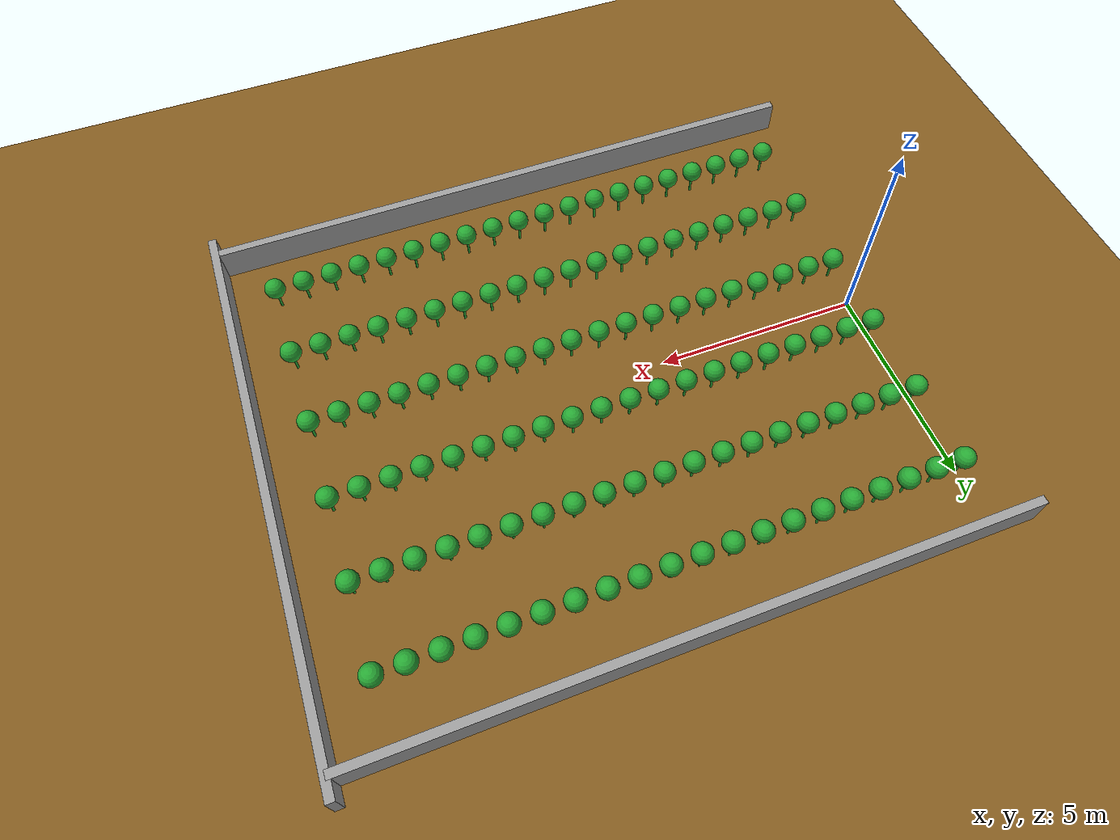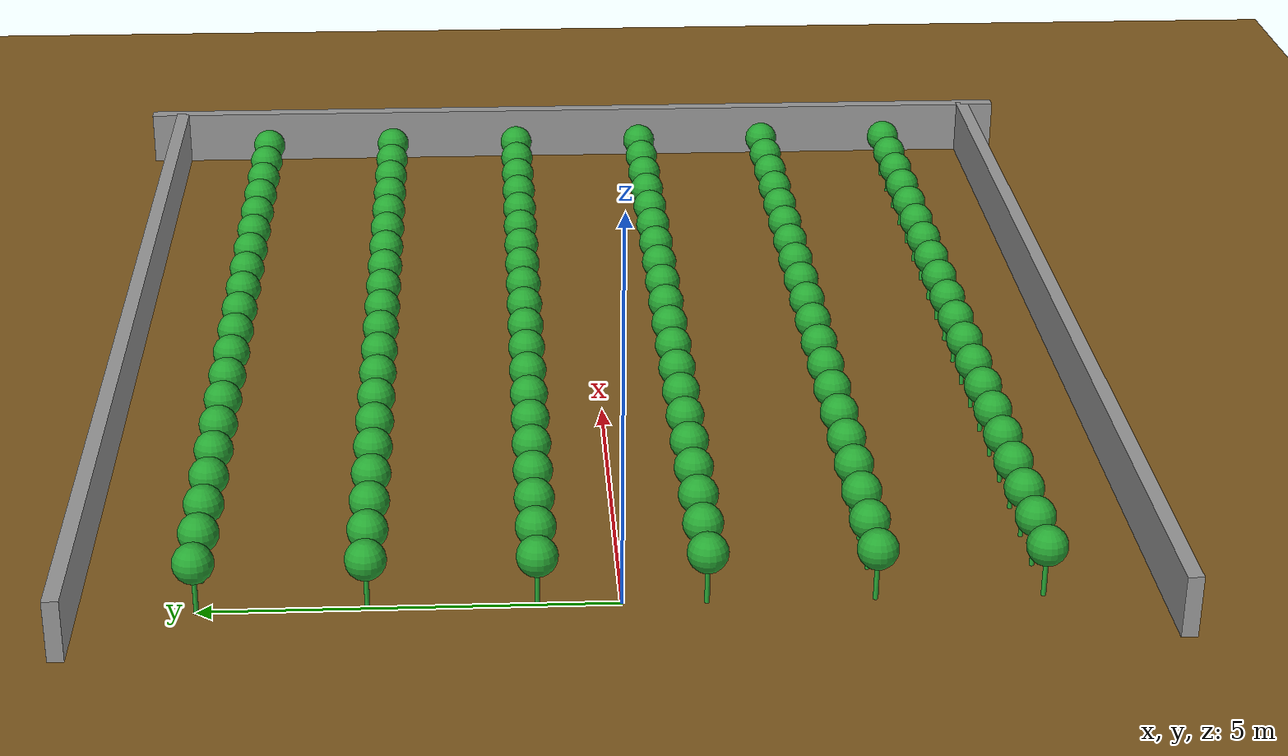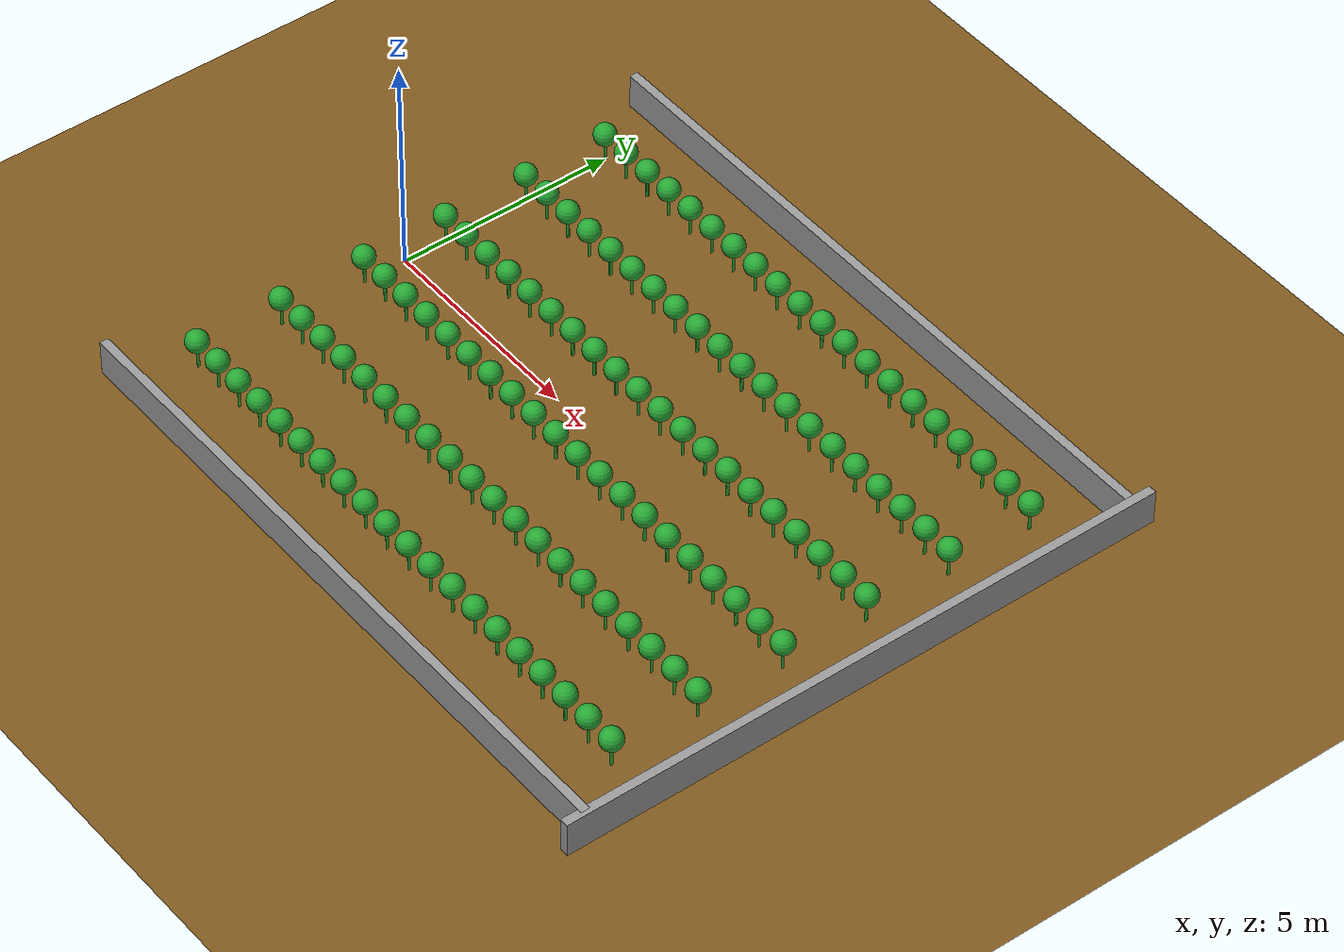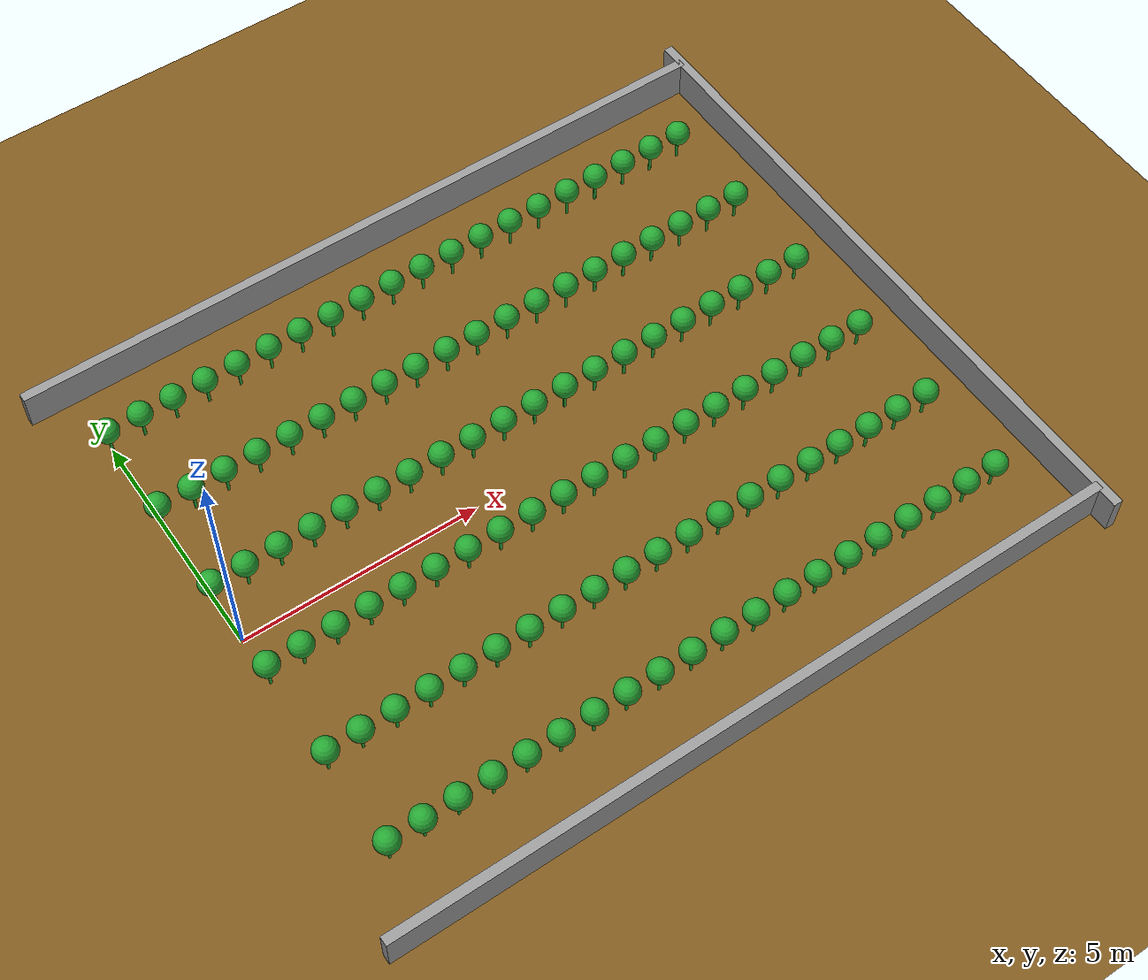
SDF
<sdf version='1.7'>
  <world name='crop_field'>

    <!-- Lighting -->
    <light name='sun' type='directional'>
      <cast_shadows>1</cast_shadows>
      <pose>0 0 10 0 -0 0</pose>
      <diffuse>0.8 0.8 0.8 1</diffuse>
      <specular>0.2 0.2 0.2 1</specular>
      <attenuation>
        <range>1000</range>
        <constant>0.9</constant>
        <linear>0.01</linear>
        <quadratic>0.001</quadratic>
      </attenuation>
      <direction>-0.5 0.1 -0.9</direction>
    </light>

    <!-- Ground plane — brown soil color -->
    <model name='ground_plane'>
      <static>1</static>
      <link name='link'>
        <collision name='collision'>
          <geometry>
            <plane><normal>0 0 1</normal><size>100 100</size></plane>
          </geometry>
          <surface><friction><ode><mu>100</mu><mu2>50</mu2></ode></friction></surface>
        </collision>
        <visual name='visual'>
          <cast_shadows>0</cast_shadows>
          <geometry>
            <plane><normal>0 0 1</normal><size>100 100</size></plane>
          </geometry>
          <material>
            <ambient>0.45 0.30 0.10 1</ambient>
            <diffuse>0.50 0.35 0.12 1</diffuse>
          </material>
        </visual>
      </link>
    </model>

    <physics type='ode'>
      <max_step_size>0.01</max_step_size>
      <real_time_factor>1</real_time_factor>
      <real_time_update_rate>100</real_time_update_rate>
    </physics>

    <scene>
      <ambient>0.4 0.4 0.4 1</ambient>
      <background>0.6 0.8 0.5 1</background>
      <shadows>1</shadows>
    </scene>

    <!-- Overhead camera — wide enough to see full 6-row field -->
    <gui fullscreen='0'>
      <camera name='user_camera'>
        <pose>6.5 0 22 0 1.5708 0</pose>
        <view_controller>orbit</view_controller>
        <projection_type>perspective</projection_type>
      </camera>
    </gui>

    <!-- ==================== ROW 1 (y = -5.0) ==================== -->
    <model name='row1_plant_00'><static>1</static><link name='link'><collision name='c'><geometry><cylinder><radius>0.05</radius><length>0.8</length></cylinder></geometry></collision><visual name='stem'><pose>0 0 -0.125 0 0 0</pose><geometry><cylinder><radius>0.03</radius><length>0.55</length></cylinder></geometry><material><script><uri>file://media/materials/scripts/gazebo.material</uri><name>Gazebo/Green</name></script></material></visual><visual name='canopy'><pose>0 0 0.275 0 0 0</pose><geometry><sphere><radius>0.25</radius></sphere></geometry><material><script><uri>file://media/materials/scripts/gazebo.material</uri><name>Gazebo/Green</name></script></material></visual></link><pose>0.0 -5.0 0.4 0 0 0</pose></model>
    <model name='row1_plant_01'><static>1</static><link name='link'><collision name='c'><geometry><cylinder><radius>0.05</radius><length>0.8</length></cylinder></geometry></collision><visual name='stem'><pose>0 0 -0.125 0 0 0</pose><geometry><cylinder><radius>0.03</radius><length>0.55</length></cylinder></geometry><material><script><uri>file://media/materials/scripts/gazebo.material</uri><name>Gazebo/Green</name></script></material></visual><visual name='canopy'><pose>0 0 0.275 0 0 0</pose><geometry><sphere><radius>0.25</radius></sphere></geometry><material><script><uri>file://media/materials/scripts/gazebo.material</uri><name>Gazebo/Green</name></script></material></visual></link><pose>0.7 -5.0 0.4 0 0 0</pose></model>
    <model name='row1_plant_02'><static>1</static><link name='link'><collision name='c'><geometry><cylinder><radius>0.05</radius><length>0.8</length></cylinder></geometry></collision><visual name='stem'><pose>0 0 -0.125 0 0 0</pose><geometry><cylinder><radius>0.03</radius><length>0.55</length></cylinder></geometry><material><script><uri>file://media/materials/scripts/gazebo.material</uri><name>Gazebo/Green</name></script></material></visual><visual name='canopy'><pose>0 0 0.275 0 0 0</pose><geometry><sphere><radius>0.25</radius></sphere></geometry><material><script><uri>file://media/materials/scripts/gazebo.material</uri><name>Gazebo/Green</name></script></material></visual></link><pose>1.4 -5.0 0.4 0 0 0</pose></model>
    <model name='row1_plant_03'><static>1</static><link name='link'><collision name='c'><geometry><cylinder><radius>0.05</radius><length>0.8</length></cylinder></geometry></collision><visual name='stem'><pose>0 0 -0.125 0 0 0</pose><geometry><cylinder><radius>0.03</radius><length>0.55</length></cylinder></geometry><material><script><uri>file://media/materials/scripts/gazebo.material</uri><name>Gazebo/Green</name></script></material></visual><visual name='canopy'><pose>0 0 0.275 0 0 0</pose><geometry><sphere><radius>0.25</radius></sphere></geometry><material><script><uri>file://media/materials/scripts/gazebo.material</uri><name>Gazebo/Green</name></script></material></visual></link><pose>2.1 -5.0 0.4 0 0 0</pose></model>
    <model name='row1_plant_04'><static>1</static><link name='link'><collision name='c'><geometry><cylinder><radius>0.05</radius><length>0.8</length></cylinder></geometry></collision><visual name='stem'><pose>0 0 -0.125 0 0 0</pose><geometry><cylinder><radius>0.03</radius><length>0.55</length></cylinder></geometry><material><script><uri>file://media/materials/scripts/gazebo.material</uri><name>Gazebo/Green</name></script></material></visual><visual name='canopy'><pose>0 0 0.275 0 0 0</pose><geometry><sphere><radius>0.25</radius></sphere></geometry><material><script><uri>file://media/materials/scripts/gazebo.material</uri><name>Gazebo/Green</name></script></material></visual></link><pose>2.8 -5.0 0.4 0 0 0</pose></model>
    <model name='row1_plant_05'><static>1</static><link name='link'><collision name='c'><geometry><cylinder><radius>0.05</radius><length>0.8</length></cylinder></geometry></collision><visual name='stem'><pose>0 0 -0.125 0 0 0</pose><geometry><cylinder><radius>0.03</radius><length>0.55</length></cylinder></geometry><material><script><uri>file://media/materials/scripts/gazebo.material</uri><name>Gazebo/Green</name></script></material></visual><visual name='canopy'><pose>0 0 0.275 0 0 0</pose><geometry><sphere><radius>0.25</radius></sphere></geometry><material><script><uri>file://media/materials/scripts/gazebo.material</uri><name>Gazebo/Green</name></script></material></visual></link><pose>3.5 -5.0 0.4 0 0 0</pose></model>
    <model name='row1_plant_06'><static>1</static><link name='link'><collision name='c'><geometry><cylinder><radius>0.05</radius><length>0.8</length></cylinder></geometry></collision><visual name='stem'><pose>0 0 -0.125 0 0 0</pose><geometry><cylinder><radius>0.03</radius><length>0.55</length></cylinder></geometry><material><script><uri>file://media/materials/scripts/gazebo.material</uri><name>Gazebo/Green</name></script></material></visual><visual name='canopy'><pose>0 0 0.275 0 0 0</pose><geometry><sphere><radius>0.25</radius></sphere></geometry><material><script><uri>file://media/materials/scripts/gazebo.material</uri><name>Gazebo/Green</name></script></material></visual></link><pose>4.2 -5.0 0.4 0 0 0</pose></model>
    <model name='row1_plant_07'><static>1</static><link name='link'><collision name='c'><geometry><cylinder><radius>0.05</radius><length>0.8</length></cylinder></geometry></collision><visual name='stem'><pose>0 0 -0.125 0 0 0</pose><geometry><cylinder><radius>0.03</radius><length>0.55</length></cylinder></geometry><material><script><uri>file://media/materials/scripts/gazebo.material</uri><name>Gazebo/Green</name></script></material></visual><visual name='canopy'><pose>0 0 0.275 0 0 0</pose><geometry><sphere><radius>0.25</radius></sphere></geometry><material><script><uri>file://media/materials/scripts/gazebo.material</uri><name>Gazebo/Green</name></script></material></visual></link><pose>4.9 -5.0 0.4 0 0 0</pose></model>
    <model name='row1_plant_08'><static>1</static><link name='link'><collision name='c'><geometry><cylinder><radius>0.05</radius><length>0.8</length></cylinder></geometry></collision><visual name='stem'><pose>0 0 -0.125 0 0 0</pose><geometry><cylinder><radius>0.03</radius><length>0.55</length></cylinder></geometry><material><script><uri>file://media/materials/scripts/gazebo.material</uri><name>Gazebo/Green</name></script></material></visual><visual name='canopy'><pose>0 0 0.275 0 0 0</pose><geometry><sphere><radius>0.25</radius></sphere></geometry><material><script><uri>file://media/materials/scripts/gazebo.material</uri><name>Gazebo/Green</name></script></material></visual></link><pose>5.6 -5.0 0.4 0 0 0</pose></model>
    <model name='row1_plant_09'><static>1</static><link name='link'><collision name='c'><geometry><cylinder><radius>0.05</radius><length>0.8</length></cylinder></geometry></collision><visual name='stem'><pose>0 0 -0.125 0 0 0</pose><geometry><cylinder><radius>0.03</radius><length>0.55</length></cylinder></geometry><material><script><uri>file://media/materials/scripts/gazebo.material</uri><name>Gazebo/Green</name></script></material></visual><visual name='canopy'><pose>0 0 0.275 0 0 0</pose><geometry><sphere><radius>0.25</radius></sphere></geometry><material><script><uri>file://media/materials/scripts/gazebo.material</uri><name>Gazebo/Green</name></script></material></visual></link><pose>6.3 -5.0 0.4 0 0 0</pose></model>
    <model name='row1_plant_10'><static>1</static><link name='link'><collision name='c'><geometry><cylinder><radius>0.05</radius><length>0.8</length></cylinder></geometry></collision><visual name='stem'><pose>0 0 -0.125 0 0 0</pose><geometry><cylinder><radius>0.03</radius><length>0.55</length></cylinder></geometry><material><script><uri>file://media/materials/scripts/gazebo.material</uri><name>Gazebo/Green</name></script></material></visual><visual name='canopy'><pose>0 0 0.275 0 0 0</pose><geometry><sphere><radius>0.25</radius></sphere></geometry><material><script><uri>file://media/materials/scripts/gazebo.material</uri><name>Gazebo/Green</name></script></material></visual></link><pose>7.0 -5.0 0.4 0 0 0</pose></model>
    <model name='row1_plant_11'><static>1</static><link name='link'><collision name='c'><geometry><cylinder><radius>0.05</radius><length>0.8</length></cylinder></geometry></collision><visual name='stem'><pose>0 0 -0.125 0 0 0</pose><geometry><cylinder><radius>0.03</radius><length>0.55</length></cylinder></geometry><material><script><uri>file://media/materials/scripts/gazebo.material</uri><name>Gazebo/Green</name></script></material></visual><visual name='canopy'><pose>0 0 0.275 0 0 0</pose><geometry><sphere><radius>0.25</radius></sphere></geometry><material><script><uri>file://media/materials/scripts/gazebo.material</uri><name>Gazebo/Green</name></script></material></visual></link><pose>7.7 -5.0 0.4 0 0 0</pose></model>
    <model name='row1_plant_12'><static>1</static><link name='link'><collision name='c'><geometry><cylinder><radius>0.05</radius><length>0.8</length></cylinder></geometry></collision><visual name='stem'><pose>0 0 -0.125 0 0 0</pose><geometry><cylinder><radius>0.03</radius><length>0.55</length></cylinder></geometry><material><script><uri>file://media/materials/scripts/gazebo.material</uri><name>Gazebo/Green</name></script></material></visual><visual name='canopy'><pose>0 0 0.275 0 0 0</pose><geometry><sphere><radius>0.25</radius></sphere></geometry><material><script><uri>file://media/materials/scripts/gazebo.material</uri><name>Gazebo/Green</name></script></material></visual></link><pose>8.4 -5.0 0.4 0 0 0</pose></model>
    <model name='row1_plant_13'><static>1</static><link name='link'><collision name='c'><geometry><cylinder><radius>0.05</radius><length>0.8</length></cylinder></geometry></collision><visual name='stem'><pose>0 0 -0.125 0 0 0</pose><geometry><cylinder><radius>0.03</radius><length>0.55</length></cylinder></geometry><material><script><uri>file://media/materials/scripts/gazebo.material</uri><name>Gazebo/Green</name></script></material></visual><visual name='canopy'><pose>0 0 0.275 0 0 0</pose><geometry><sphere><radius>0.25</radius></sphere></geometry><material><script><uri>file://media/materials/scripts/gazebo.material</uri><name>Gazebo/Green</name></script></material></visual></link><pose>9.1 -5.0 0.4 0 0 0</pose></model>
    <model name='row1_plant_14'><static>1</static><link name='link'><collision name='c'><geometry><cylinder><radius>0.05</radius><length>0.8</length></cylinder></geometry></collision><visual name='stem'><pose>0 0 -0.125 0 0 0</pose><geometry><cylinder><radius>0.03</radius><length>0.55</length></cylinder></geometry><material><script><uri>file://media/materials/scripts/gazebo.material</uri><name>Gazebo/Green</name></script></material></visual><visual name='canopy'><pose>0 0 0.275 0 0 0</pose><geometry><sphere><radius>0.25</radius></sphere></geometry><material><script><uri>file://media/materials/scripts/gazebo.material</uri><name>Gazebo/Green</name></script></material></visual></link><pose>9.8 -5.0 0.4 0 0 0</pose></model>
    <model name='row1_plant_15'><static>1</static><link name='link'><collision name='c'><geometry><cylinder><radius>0.05</radius><length>0.8</length></cylinder></geometry></collision><visual name='stem'><pose>0 0 -0.125 0 0 0</pose><geometry><cylinder><radius>0.03</radius><length>0.55</length></cylinder></geometry><material><script><uri>file://media/materials/scripts/gazebo.material</uri><name>Gazebo/Green</name></script></material></visual><visual name='canopy'><pose>0 0 0.275 0 0 0</pose><geometry><sphere><radius>0.25</radius></sphere></geometry><material><script><uri>file://media/materials/scripts/gazebo.material</uri><name>Gazebo/Green</name></script></material></visual></link><pose>10.5 -5.0 0.4 0 0 0</pose></model>
    <model name='row1_plant_16'><static>1</static><link name='link'><collision name='c'><geometry><cylinder><radius>0.05</radius><length>0.8</length></cylinder></geometry></collision><visual name='stem'><pose>0 0 -0.125 0 0 0</pose><geometry><cylinder><radius>0.03</radius><length>0.55</length></cylinder></geometry><material><script><uri>file://media/materials/scripts/gazebo.material</uri><name>Gazebo/Green</name></script></material></visual><visual name='canopy'><pose>0 0 0.275 0 0 0</pose><geometry><sphere><radius>0.25</radius></sphere></geometry><material><script><uri>file://media/materials/scripts/gazebo.material</uri><name>Gazebo/Green</name></script></material></visual></link><pose>11.2 -5.0 0.4 0 0 0</pose></model>
    <model name='row1_plant_17'><static>1</static><link name='link'><collision name='c'><geometry><cylinder><radius>0.05</radius><length>0.8</length></cylinder></geometry></collision><visual name='stem'><pose>0 0 -0.125 0 0 0</pose><geometry><cylinder><radius>0.03</radius><length>0.55</length></cylinder></geometry><material><script><uri>file://media/materials/scripts/gazebo.material</uri><name>Gazebo/Green</name></script></material></visual><visual name='canopy'><pose>0 0 0.275 0 0 0</pose><geometry><sphere><radius>0.25</radius></sphere></geometry><material><script><uri>file://media/materials/scripts/gazebo.material</uri><name>Gazebo/Green</name></script></material></visual></link><pose>11.9 -5.0 0.4 0 0 0</pose></model>
    <model name='row1_plant_18'><static>1</static><link name='link'><collision name='c'><geometry><cylinder><radius>0.05</radius><length>0.8</length></cylinder></geometry></collision><visual name='stem'><pose>0 0 -0.125 0 0 0</pose><geometry><cylinder><radius>0.03</radius><length>0.55</length></cylinder></geometry><material><script><uri>file://media/materials/scripts/gazebo.material</uri><name>Gazebo/Green</name></script></material></visual><visual name='canopy'><pose>0 0 0.275 0 0 0</pose><geometry><sphere><radius>0.25</radius></sphere></geometry><material><script><uri>file://media/materials/scripts/gazebo.material</uri><name>Gazebo/Green</name></script></material></visual></link><pose>12.6 -5.0 0.4 0 0 0</pose></model>
    <model name='row1_plant_19'><static>1</static><link name='link'><collision name='c'><geometry><cylinder><radius>0.05</radius><length>0.8</length></cylinder></geometry></collision><visual name='stem'><pose>0 0 -0.125 0 0 0</pose><geometry><cylinder><radius>0.03</radius><length>0.55</length></cylinder></geometry><material><script><uri>file://media/materials/scripts/gazebo.material</uri><name>Gazebo/Green</name></script></material></visual><visual name='canopy'><pose>0 0 0.275 0 0 0</pose><geometry><sphere><radius>0.25</radius></sphere></geometry><material><script><uri>file://media/materials/scripts/gazebo.material</uri><name>Gazebo/Green</name></script></material></visual></link><pose>13.3 -5.0 0.4 0 0 0</pose></model>

    <!-- ==================== ROW 2 (y = -3.0) ==================== -->
    <model name='row2_plant_00'><static>1</static><link name='link'><collision name='c'><geometry><cylinder><radius>0.05</radius><length>0.8</length></cylinder></geometry></collision><visual name='stem'><pose>0 0 -0.125 0 0 0</pose><geometry><cylinder><radius>0.03</radius><length>0.55</length></cylinder></geometry><material><script><uri>file://media/materials/scripts/gazebo.material</uri><name>Gazebo/Green</name></script></material></visual><visual name='canopy'><pose>0 0 0.275 0 0 0</pose><geometry><sphere><radius>0.25</radius></sphere></geometry><material><script><uri>file://media/materials/scripts/gazebo.material</uri><name>Gazebo/Green</name></script></material></visual></link><pose>0.0 -3.0 0.4 0 0 0</pose></model>
    <model name='row2_plant_01'><static>1</static><link name='link'><collision name='c'><geometry><cylinder><radius>0.05</radius><length>0.8</length></cylinder></geometry></collision><visual name='stem'><pose>0 0 -0.125 0 0 0</pose><geometry><cylinder><radius>0.03</radius><length>0.55</length></cylinder></geometry><material><script><uri>file://media/materials/scripts/gazebo.material</uri><name>Gazebo/Green</name></script></material></visual><visual name='canopy'><pose>0 0 0.275 0 0 0</pose><geometry><sphere><radius>0.25</radius></sphere></geometry><material><script><uri>file://media/materials/scripts/gazebo.material</uri><name>Gazebo/Green</name></script></material></visual></link><pose>0.7 -3.0 0.4 0 0 0</pose></model>
    <model name='row2_plant_02'><static>1</static><link name='link'><collision name='c'><geometry><cylinder><radius>0.05</radius><length>0.8</length></cylinder></geometry></collision><visual name='stem'><pose>0 0 -0.125 0 0 0</pose><geometry><cylinder><radius>0.03</radius><length>0.55</length></cylinder></geometry><material><script><uri>file://media/materials/scripts/gazebo.material</uri><name>Gazebo/Green</name></script></material></visual><visual name='canopy'><pose>0 0 0.275 0 0 0</pose><geometry><sphere><radius>0.25</radius></sphere></geometry><material><script><uri>file://media/materials/scripts/gazebo.material</uri><name>Gazebo/Green</name></script></material></visual></link><pose>1.4 -3.0 0.4 0 0 0</pose></model>
    <model name='row2_plant_03'><static>1</static><link name='link'><collision name='c'><geometry><cylinder><radius>0.05</radius><length>0.8</length></cylinder></geometry></collision><visual name='stem'><pose>0 0 -0.125 0 0 0</pose><geometry><cylinder><radius>0.03</radius><length>0.55</length></cylinder></geometry><material><script><uri>file://media/materials/scripts/gazebo.material</uri><name>Gazebo/Green</name></script></material></visual><visual name='canopy'><pose>0 0 0.275 0 0 0</pose><geometry><sphere><radius>0.25</radius></sphere></geometry><material><script><uri>file://media/materials/scripts/gazebo.material</uri><name>Gazebo/Green</name></script></material></visual></link><pose>2.1 -3.0 0.4 0 0 0</pose></model>
    <model name='row2_plant_04'><static>1</static><link name='link'><collision name='c'><geometry><cylinder><radius>0.05</radius><length>0.8</length></cylinder></geometry></collision><visual name='stem'><pose>0 0 -0.125 0 0 0</pose><geometry><cylinder><radius>0.03</radius><length>0.55</length></cylinder></geometry><material><script><uri>file://media/materials/scripts/gazebo.material</uri><name>Gazebo/Green</name></script></material></visual><visual name='canopy'><pose>0 0 0.275 0 0 0</pose><geometry><sphere><radius>0.25</radius></sphere></geometry><material><script><uri>file://media/materials/scripts/gazebo.material</uri><name>Gazebo/Green</name></script></material></visual></link><pose>2.8 -3.0 0.4 0 0 0</pose></model>
    <model name='row2_plant_05'><static>1</static><link name='link'><collision name='c'><geometry><cylinder><radius>0.05</radius><length>0.8</length></cylinder></geometry></collision><visual name='stem'><pose>0 0 -0.125 0 0 0</pose><geometry><cylinder><radius>0.03</radius><length>0.55</length></cylinder></geometry><material><script><uri>file://media/materials/scripts/gazebo.material</uri><name>Gazebo/Green</name></script></material></visual><visual name='canopy'><pose>0 0 0.275 0 0 0</pose><geometry><sphere><radius>0.25</radius></sphere></geometry><material><script><uri>file://media/materials/scripts/gazebo.material</uri><name>Gazebo/Green</name></script></material></visual></link><pose>3.5 -3.0 0.4 0 0 0</pose></model>
    <model name='row2_plant_06'><static>1</static><link name='link'><collision name='c'><geometry><cylinder><radius>0.05</radius><length>0.8</length></cylinder></geometry></collision><visual name='stem'><pose>0 0 -0.125 0 0 0</pose><geometry><cylinder><radius>0.03</radius><length>0.55</length></cylinder></geometry><material><script><uri>file://media/materials/scripts/gazebo.material</uri><name>Gazebo/Green</name></script></material></visual><visual name='canopy'><pose>0 0 0.275 0 0 0</pose><geometry><sphere><radius>0.25</radius></sphere></geometry><material><script><uri>file://media/materials/scripts/gazebo.material</uri><name>Gazebo/Green</name></script></material></visual></link><pose>4.2 -3.0 0.4 0 0 0</pose></model>
    <model name='row2_plant_07'><static>1</static><link name='link'><collision name='c'><geometry><cylinder><radius>0.05</radius><length>0.8</length></cylinder></geometry></collision><visual name='stem'><pose>0 0 -0.125 0 0 0</pose><geometry><cylinder><radius>0.03</radius><length>0.55</length></cylinder></geometry><material><script><uri>file://media/materials/scripts/gazebo.material</uri><name>Gazebo/Green</name></script></material></visual><visual name='canopy'><pose>0 0 0.275 0 0 0</pose><geometry><sphere><radius>0.25</radius></sphere></geometry><material><script><uri>file://media/materials/scripts/gazebo.material</uri><name>Gazebo/Green</name></script></material></visual></link><pose>4.9 -3.0 0.4 0 0 0</pose></model>
    <model name='row2_plant_08'><static>1</static><link name='link'><collision name='c'><geometry><cylinder><radius>0.05</radius><length>0.8</length></cylinder></geometry></collision><visual name='stem'><pose>0 0 -0.125 0 0 0</pose><geometry><cylinder><radius>0.03</radius><length>0.55</length></cylinder></geometry><material><script><uri>file://media/materials/scripts/gazebo.material</uri><name>Gazebo/Green</name></script></material></visual><visual name='canopy'><pose>0 0 0.275 0 0 0</pose><geometry><sphere><radius>0.25</radius></sphere></geometry><material><script><uri>file://media/materials/scripts/gazebo.material</uri><name>Gazebo/Green</name></script></material></visual></link><pose>5.6 -3.0 0.4 0 0 0</pose></model>
    <model name='row2_plant_09'><static>1</static><link name='link'><collision name='c'><geometry><cylinder><radius>0.05</radius><length>0.8</length></cylinder></geometry></collision><visual name='stem'><pose>0 0 -0.125 0 0 0</pose><geometry><cylinder><radius>0.03</radius><length>0.55</length></cylinder></geometry><material><script><uri>file://media/materials/scripts/gazebo.material</uri><name>Gazebo/Green</name></script></material></visual><visual name='canopy'><pose>0 0 0.275 0 0 0</pose><geometry><sphere><radius>0.25</radius></sphere></geometry><material><script><uri>file://media/materials/scripts/gazebo.material</uri><name>Gazebo/Green</name></script></material></visual></link><pose>6.3 -3.0 0.4 0 0 0</pose></model>
    <model name='row2_plant_10'><static>1</static><link name='link'><collision name='c'><geometry><cylinder><radius>0.05</radius><length>0.8</length></cylinder></geometry></collision><visual name='stem'><pose>0 0 -0.125 0 0 0</pose><geometry><cylinder><radius>0.03</radius><length>0.55</length></cylinder></geometry><material><script><uri>file://media/materials/scripts/gazebo.material</uri><name>Gazebo/Green</name></script></material></visual><visual name='canopy'><pose>0 0 0.275 0 0 0</pose><geometry><sphere><radius>0.25</radius></sphere></geometry><material><script><uri>file://media/materials/scripts/gazebo.material</uri><name>Gazebo/Green</name></script></material></visual></link><pose>7.0 -3.0 0.4 0 0 0</pose></model>
    <model name='row2_plant_11'><static>1</static><link name='link'><collision name='c'><geometry><cylinder><radius>0.05</radius><length>0.8</length></cylinder></geometry></collision><visual name='stem'><pose>0 0 -0.125 0 0 0</pose><geometry><cylinder><radius>0.03</radius><length>0.55</length></cylinder></geometry><material><script><uri>file://media/materials/scripts/gazebo.material</uri><name>Gazebo/Green</name></script></material></visual><visual name='canopy'><pose>0 0 0.275 0 0 0</pose><geometry><sphere><radius>0.25</radius></sphere></geometry><material><script><uri>file://media/materials/scripts/gazebo.material</uri><name>Gazebo/Green</name></script></material></visual></link><pose>7.7 -3.0 0.4 0 0 0</pose></model>
    <model name='row2_plant_12'><static>1</static><link name='link'><collision name='c'><geometry><cylinder><radius>0.05</radius><length>0.8</length></cylinder></geometry></collision><visual name='stem'><pose>0 0 -0.125 0 0 0</pose><geometry><cylinder><radius>0.03</radius><length>0.55</length></cylinder></geometry><material><script><uri>file://media/materials/scripts/gazebo.material</uri><name>Gazebo/Green</name></script></material></visual><visual name='canopy'><pose>0 0 0.275 0 0 0</pose><geometry><sphere><radius>0.25</radius></sphere></geometry><material><script><uri>file://media/materials/scripts/gazebo.material</uri><name>Gazebo/Green</name></script></material></visual></link><pose>8.4 -3.0 0.4 0 0 0</pose></model>
    <model name='row2_plant_13'><static>1</static><link name='link'><collision name='c'><geometry><cylinder><radius>0.05</radius><length>0.8</length></cylinder></geometry></collision><visual name='stem'><pose>0 0 -0.125 0 0 0</pose><geometry><cylinder><radius>0.03</radius><length>0.55</length></cylinder></geometry><material><script><uri>file://media/materials/scripts/gazebo.material</uri><name>Gazebo/Green</name></script></material></visual><visual name='canopy'><pose>0 0 0.275 0 0 0</pose><geometry><sphere><radius>0.25</radius></sphere></geometry><material><script><uri>file://media/materials/scripts/gazebo.material</uri><name>Gazebo/Green</name></script></material></visual></link><pose>9.1 -3.0 0.4 0 0 0</pose></model>
    <model name='row2_plant_14'><static>1</static><link name='link'><collision name='c'><geometry><cylinder><radius>0.05</radius><length>0.8</length></cylinder></geometry></collision><visual name='stem'><pose>0 0 -0.125 0 0 0</pose><geometry><cylinder><radius>0.03</radius><length>0.55</length></cylinder></geometry><material><script><uri>file://media/materials/scripts/gazebo.material</uri><name>Gazebo/Green</name></script></material></visual><visual name='canopy'><pose>0 0 0.275 0 0 0</pose><geometry><sphere><radius>0.25</radius></sphere></geometry><material><script><uri>file://media/materials/scripts/gazebo.material</uri><name>Gazebo/Green</name></script></material></visual></link><pose>9.8 -3.0 0.4 0 0 0</pose></model>
    <model name='row2_plant_15'><static>1</static><link name='link'><collision name='c'><geometry><cylinder><radius>0.05</radius><length>0.8</length></cylinder></geometry></collision><visual name='stem'><pose>0 0 -0.125 0 0 0</pose><geometry><cylinder><radius>0.03</radius><length>0.55</length></cylinder></geometry><material><script><uri>file://media/materials/scripts/gazebo.material</uri><name>Gazebo/Green</name></script></material></visual><visual name='canopy'><pose>0 0 0.275 0 0 0</pose><geometry><sphere><radius>0.25</radius></sphere></geometry><material><script><uri>file://media/materials/scripts/gazebo.material</uri><name>Gazebo/Green</name></script></material></visual></link><pose>10.5 -3.0 0.4 0 0 0</pose></model>
    <model name='row2_plant_16'><static>1</static><link name='link'><collision name='c'><geometry><cylinder><radius>0.05</radius><length>0.8</length></cylinder></geometry></collision><visual name='stem'><pose>0 0 -0.125 0 0 0</pose><geometry><cylinder><radius>0.03</radius><length>0.55</length></cylinder></geometry><material><script><uri>file://media/materials/scripts/gazebo.material</uri><name>Gazebo/Green</name></script></material></visual><visual name='canopy'><pose>0 0 0.275 0 0 0</pose><geometry><sphere><radius>0.25</radius></sphere></geometry><material><script><uri>file://media/materials/scripts/gazebo.material</uri><name>Gazebo/Green</name></script></material></visual></link><pose>11.2 -3.0 0.4 0 0 0</pose></model>
    <model name='row2_plant_17'><static>1</static><link name='link'><collision name='c'><geometry><cylinder><radius>0.05</radius><length>0.8</length></cylinder></geometry></collision><visual name='stem'><pose>0 0 -0.125 0 0 0</pose><geometry><cylinder><radius>0.03</radius><length>0.55</length></cylinder></geometry><material><script><uri>file://media/materials/scripts/gazebo.material</uri><name>Gazebo/Green</name></script></material></visual><visual name='canopy'><pose>0 0 0.275 0 0 0</pose><geometry><sphere><radius>0.25</radius></sphere></geometry><material><script><uri>file://media/materials/scripts/gazebo.material</uri><name>Gazebo/Green</name></script></material></visual></link><pose>11.9 -3.0 0.4 0 0 0</pose></model>
    <model name='row2_plant_18'><static>1</static><link name='link'><collision name='c'><geometry><cylinder><radius>0.05</radius><length>0.8</length></cylinder></geometry></collision><visual name='stem'><pose>0 0 -0.125 0 0 0</pose><geometry><cylinder><radius>0.03</radius><length>0.55</length></cylinder></geometry><material><script><uri>file://media/materials/scripts/gazebo.material</uri><name>Gazebo/Green</name></script></material></visual><visual name='canopy'><pose>0 0 0.275 0 0 0</pose><geometry><sphere><radius>0.25</radius></sphere></geometry><material><script><uri>file://media/materials/scripts/gazebo.material</uri><name>Gazebo/Green</name></script></material></visual></link><pose>12.6 -3.0 0.4 0 0 0</pose></model>
    <model name='row2_plant_19'><static>1</static><link name='link'><collision name='c'><geometry><cylinder><radius>0.05</radius><length>0.8</length></cylinder></geometry></collision><visual name='stem'><pose>0 0 -0.125 0 0 0</pose><geometry><cylinder><radius>0.03</radius><length>0.55</length></cylinder></geometry><material><script><uri>file://media/materials/scripts/gazebo.material</uri><name>Gazebo/Green</name></script></material></visual><visual name='canopy'><pose>0 0 0.275 0 0 0</pose><geometry><sphere><radius>0.25</radius></sphere></geometry><material><script><uri>file://media/materials/scripts/gazebo.material</uri><name>Gazebo/Green</name></script></material></visual></link><pose>13.3 -3.0 0.4 0 0 0</pose></model>

    <!-- ==================== ROW 3 (y = -1.0) ==================== -->
    <model name='row3_plant_00'><static>1</static><link name='link'><collision name='c'><geometry><cylinder><radius>0.05</radius><length>0.8</length></cylinder></geometry></collision><visual name='stem'><pose>0 0 -0.125 0 0 0</pose><geometry><cylinder><radius>0.03</radius><length>0.55</length></cylinder></geometry><material><script><uri>file://media/materials/scripts/gazebo.material</uri><name>Gazebo/Green</name></script></material></visual><visual name='canopy'><pose>0 0 0.275 0 0 0</pose><geometry><sphere><radius>0.25</radius></sphere></geometry><material><script><uri>file://media/materials/scripts/gazebo.material</uri><name>Gazebo/Green</name></script></material></visual></link><pose>0.0 -1.0 0.4 0 0 0</pose></model>
    <model name='row3_plant_01'><static>1</static><link name='link'><collision name='c'><geometry><cylinder><radius>0.05</radius><length>0.8</length></cylinder></geometry></collision><visual name='stem'><pose>0 0 -0.125 0 0 0</pose><geometry><cylinder><radius>0.03</radius><length>0.55</length></cylinder></geometry><material><script><uri>file://media/materials/scripts/gazebo.material</uri><name>Gazebo/Green</name></script></material></visual><visual name='canopy'><pose>0 0 0.275 0 0 0</pose><geometry><sphere><radius>0.25</radius></sphere></geometry><material><script><uri>file://media/materials/scripts/gazebo.material</uri><name>Gazebo/Green</name></script></material></visual></link><pose>0.7 -1.0 0.4 0 0 0</pose></model>
    <model name='row3_plant_02'><static>1</static><link name='link'><collision name='c'><geometry><cylinder><radius>0.05</radius><length>0.8</length></cylinder></geometry></collision><visual name='stem'><pose>0 0 -0.125 0 0 0</pose><geometry><cylinder><radius>0.03</radius><length>0.55</length></cylinder></geometry><material><script><uri>file://media/materials/scripts/gazebo.material</uri><name>Gazebo/Green</name></script></material></visual><visual name='canopy'><pose>0 0 0.275 0 0 0</pose><geometry><sphere><radius>0.25</radius></sphere></geometry><material><script><uri>file://media/materials/scripts/gazebo.material</uri><name>Gazebo/Green</name></script></material></visual></link><pose>1.4 -1.0 0.4 0 0 0</pose></model>
    <model name='row3_plant_03'><static>1</static><link name='link'><collision name='c'><geometry><cylinder><radius>0.05</radius><length>0.8</length></cylinder></geometry></collision><visual name='stem'><pose>0 0 -0.125 0 0 0</pose><geometry><cylinder><radius>0.03</radius><length>0.55</length></cylinder></geometry><material><script><uri>file://media/materials/scripts/gazebo.material</uri><name>Gazebo/Green</name></script></material></visual><visual name='canopy'><pose>0 0 0.275 0 0 0</pose><geometry><sphere><radius>0.25</radius></sphere></geometry><material><script><uri>file://media/materials/scripts/gazebo.material</uri><name>Gazebo/Green</name></script></material></visual></link><pose>2.1 -1.0 0.4 0 0 0</pose></model>
    <model name='row3_plant_04'><static>1</static><link name='link'><collision name='c'><geometry><cylinder><radius>0.05</radius><length>0.8</length></cylinder></geometry></collision><visual name='stem'><pose>0 0 -0.125 0 0 0</pose><geometry><cylinder><radius>0.03</radius><length>0.55</length></cylinder></geometry><material><script><uri>file://media/materials/scripts/gazebo.material</uri><name>Gazebo/Green</name></script></material></visual><visual name='canopy'><pose>0 0 0.275 0 0 0</pose><geometry><sphere><radius>0.25</radius></sphere></geometry><material><script><uri>file://media/materials/scripts/gazebo.material</uri><name>Gazebo/Green</name></script></material></visual></link><pose>2.8 -1.0 0.4 0 0 0</pose></model>
    <model name='row3_plant_05'><static>1</static><link name='link'><collision name='c'><geometry><cylinder><radius>0.05</radius><length>0.8</length></cylinder></geometry></collision><visual name='stem'><pose>0 0 -0.125 0 0 0</pose><geometry><cylinder><radius>0.03</radius><length>0.55</length></cylinder></geometry><material><script><uri>file://media/materials/scripts/gazebo.material</uri><name>Gazebo/Green</name></script></material></visual><visual name='canopy'><pose>0 0 0.275 0 0 0</pose><geometry><sphere><radius>0.25</radius></sphere></geometry><material><script><uri>file://media/materials/scripts/gazebo.material</uri><name>Gazebo/Green</name></script></material></visual></link><pose>3.5 -1.0 0.4 0 0 0</pose></model>
    <model name='row3_plant_06'><static>1</static><link name='link'><collision name='c'><geometry><cylinder><radius>0.05</radius><length>0.8</length></cylinder></geometry></collision><visual name='stem'><pose>0 0 -0.125 0 0 0</pose><geometry><cylinder><radius>0.03</radius><length>0.55</length></cylinder></geometry><material><script><uri>file://media/materials/scripts/gazebo.material</uri><name>Gazebo/Green</name></script></material></visual><visual name='canopy'><pose>0 0 0.275 0 0 0</pose><geometry><sphere><radius>0.25</radius></sphere></geometry><material><script><uri>file://media/materials/scripts/gazebo.material</uri><name>Gazebo/Green</name></script></material></visual></link><pose>4.2 -1.0 0.4 0 0 0</pose></model>
    <model name='row3_plant_07'><static>1</static><link name='link'><collision name='c'><geometry><cylinder><radius>0.05</radius><length>0.8</length></cylinder></geometry></collision><visual name='stem'><pose>0 0 -0.125 0 0 0</pose><geometry><cylinder><radius>0.03</radius><length>0.55</length></cylinder></geometry><material><script><uri>file://media/materials/scripts/gazebo.material</uri><name>Gazebo/Green</name></script></material></visual><visual name='canopy'><pose>0 0 0.275 0 0 0</pose><geometry><sphere><radius>0.25</radius></sphere></geometry><material><script><uri>file://media/materials/scripts/gazebo.material</uri><name>Gazebo/Green</name></script></material></visual></link><pose>4.9 -1.0 0.4 0 0 0</pose></model>
    <model name='row3_plant_08'><static>1</static><link name='link'><collision name='c'><geometry><cylinder><radius>0.05</radius><length>0.8</length></cylinder></geometry></collision><visual name='stem'><pose>0 0 -0.125 0 0 0</pose><geometry><cylinder><radius>0.03</radius><length>0.55</length></cylinder></geometry><material><script><uri>file://media/materials/scripts/gazebo.material</uri><name>Gazebo/Green</name></script></material></visual><visual name='canopy'><pose>0 0 0.275 0 0 0</pose><geometry><sphere><radius>0.25</radius></sphere></geometry><material><script><uri>file://media/materials/scripts/gazebo.material</uri><name>Gazebo/Green</name></script></material></visual></link><pose>5.6 -1.0 0.4 0 0 0</pose></model>
    <model name='row3_plant_09'><static>1</static><link name='link'><collision name='c'><geometry><cylinder><radius>0.05</radius><length>0.8</length></cylinder></geometry></collision><visual name='stem'><pose>0 0 -0.125 0 0 0</pose><geometry><cylinder><radius>0.03</radius><length>0.55</length></cylinder></geometry><material><script><uri>file://media/materials/scripts/gazebo.material</uri><name>Gazebo/Green</name></script></material></visual><visual name='canopy'><pose>0 0 0.275 0 0 0</pose><geometry><sphere><radius>0.25</radius></sphere></geometry><material><script><uri>file://media/materials/scripts/gazebo.material</uri><name>Gazebo/Green</name></script></material></visual></link><pose>6.3 -1.0 0.4 0 0 0</pose></model>
    <model name='row3_plant_10'><static>1</static><link name='link'><collision name='c'><geometry><cylinder><radius>0.05</radius><length>0.8</length></cylinder></geometry></collision><visual name='stem'><pose>0 0 -0.125 0 0 0</pose><geometry><cylinder><radius>0.03</radius><length>0.55</length></cylinder></geometry><material><script><uri>file://media/materials/scripts/gazebo.material</uri><name>Gazebo/Green</name></script></material></visual><visual name='canopy'><pose>0 0 0.275 0 0 0</pose><geometry><sphere><radius>0.25</radius></sphere></geometry><material><script><uri>file://media/materials/scripts/gazebo.material</uri><name>Gazebo/Green</name></script></material></visual></link><pose>7.0 -1.0 0.4 0 0 0</pose></model>
    <model name='row3_plant_11'><static>1</static><link name='link'><collision name='c'><geometry><cylinder><radius>0.05</radius><length>0.8</length></cylinder></geometry></collision><visual name='stem'><pose>0 0 -0.125 0 0 0</pose><geometry><cylinder><radius>0.03</radius><length>0.55</length></cylinder></geometry><material><script><uri>file://media/materials/scripts/gazebo.material</uri><name>Gazebo/Green</name></script></material></visual><visual name='canopy'><pose>0 0 0.275 0 0 0</pose><geometry><sphere><radius>0.25</radius></sphere></geometry><material><script><uri>file://media/materials/scripts/gazebo.material</uri><name>Gazebo/Green</name></script></material></visual></link><pose>7.7 -1.0 0.4 0 0 0</pose></model>
    <model name='row3_plant_12'><static>1</static><link name='link'><collision name='c'><geometry><cylinder><radius>0.05</radius><length>0.8</length></cylinder></geometry></collision><visual name='stem'><pose>0 0 -0.125 0 0 0</pose><geometry><cylinder><radius>0.03</radius><length>0.55</length></cylinder></geometry><material><script><uri>file://media/materials/scripts/gazebo.material</uri><name>Gazebo/Green</name></script></material></visual><visual name='canopy'><pose>0 0 0.275 0 0 0</pose><geometry><sphere><radius>0.25</radius></sphere></geometry><material><script><uri>file://media/materials/scripts/gazebo.material</uri><name>Gazebo/Green</name></script></material></visual></link><pose>8.4 -1.0 0.4 0 0 0</pose></model>
    <model name='row3_plant_13'><static>1</static><link name='link'><collision name='c'><geometry><cylinder><radius>0.05</radius><length>0.8</length></cylinder></geometry></collision><visual name='stem'><pose>0 0 -0.125 0 0 0</pose><geometry><cylinder><radius>0.03</radius><length>0.55</length></cylinder></geometry><material><script><uri>file://media/materials/scripts/gazebo.material</uri><name>Gazebo/Green</name></script></material></visual><visual name='canopy'><pose>0 0 0.275 0 0 0</pose><geometry><sphere><radius>0.25</radius></sphere></geometry><material><script><uri>file://media/materials/scripts/gazebo.material</uri><name>Gazebo/Green</name></script></material></visual></link><pose>9.1 -1.0 0.4 0 0 0</pose></model>
    <model name='row3_plant_14'><static>1</static><link name='link'><collision name='c'><geometry><cylinder><radius>0.05</radius><length>0.8</length></cylinder></geometry></collision><visual name='stem'><pose>0 0 -0.125 0 0 0</pose><geometry><cylinder><radius>0.03</radius><length>0.55</length></cylinder></geometry><material><script><uri>file://media/materials/scripts/gazebo.material</uri><name>Gazebo/Green</name></script></material></visual><visual name='canopy'><pose>0 0 0.275 0 0 0</pose><geometry><sphere><radius>0.25</radius></sphere></geometry><material><script><uri>file://media/materials/scripts/gazebo.material</uri><name>Gazebo/Green</name></script></material></visual></link><pose>9.8 -1.0 0.4 0 0 0</pose></model>
    <model name='row3_plant_15'><static>1</static><link name='link'><collision name='c'><geometry><cylinder><radius>0.05</radius><length>0.8</length></cylinder></geometry></collision><visual name='stem'><pose>0 0 -0.125 0 0 0</pose><geometry><cylinder><radius>0.03</radius><length>0.55</length></cylinder></geometry><material><script><uri>file://media/materials/scripts/gazebo.material</uri><name>Gazebo/Green</name></script></material></visual><visual name='canopy'><pose>0 0 0.275 0 0 0</pose><geometry><sphere><radius>0.25</radius></sphere></geometry><material><script><uri>file://media/materials/scripts/gazebo.material</uri><name>Gazebo/Green</name></script></material></visual></link><pose>10.5 -1.0 0.4 0 0 0</pose></model>
    <model name='row3_plant_16'><static>1</static><link name='link'><collision name='c'><geometry><cylinder><radius>0.05</radius><length>0.8</length></cylinder></geometry></collision><visual name='stem'><pose>0 0 -0.125 0 0 0</pose><geometry><cylinder><radius>0.03</radius><length>0.55</length></cylinder></geometry><material><script><uri>file://media/materials/scripts/gazebo.material</uri><name>Gazebo/Green</name></script></material></visual><visual name='canopy'><pose>0 0 0.275 0 0 0</pose><geometry><sphere><radius>0.25</radius></sphere></geometry><material><script><uri>file://media/materials/scripts/gazebo.material</uri><name>Gazebo/Green</name></script></material></visual></link><pose>11.2 -1.0 0.4 0 0 0</pose></model>
    <model name='row3_plant_17'><static>1</static><link name='link'><collision name='c'><geometry><cylinder><radius>0.05</radius><length>0.8</length></cylinder></geometry></collision><visual name='stem'><pose>0 0 -0.125 0 0 0</pose><geometry><cylinder><radius>0.03</radius><length>0.55</length></cylinder></geometry><material><script><uri>file://media/materials/scripts/gazebo.material</uri><name>Gazebo/Green</name></script></material></visual><visual name='canopy'><pose>0 0 0.275 0 0 0</pose><geometry><sphere><radius>0.25</radius></sphere></geometry><material><script><uri>file://media/materials/scripts/gazebo.material</uri><name>Gazebo/Green</name></script></material></visual></link><pose>11.9 -1.0 0.4 0 0 0</pose></model>
    <model name='row3_plant_18'><static>1</static><link name='link'><collision name='c'><geometry><cylinder><radius>0.05</radius><length>0.8</length></cylinder></geometry></collision><visual name='stem'><pose>0 0 -0.125 0 0 0</pose><geometry><cylinder><radius>0.03</radius><length>0.55</length></cylinder></geometry><material><script><uri>file://media/materials/scripts/gazebo.material</uri><name>Gazebo/Green</name></script></material></visual><visual name='canopy'><pose>0 0 0.275 0 0 0</pose><geometry><sphere><radius>0.25</radius></sphere></geometry><material><script><uri>file://media/materials/scripts/gazebo.material</uri><name>Gazebo/Green</name></script></material></visual></link><pose>12.6 -1.0 0.4 0 0 0</pose></model>
    <model name='row3_plant_19'><static>1</static><link name='link'><collision name='c'><geometry><cylinder><radius>0.05</radius><length>0.8</length></cylinder></geometry></collision><visual name='stem'><pose>0 0 -0.125 0 0 0</pose><geometry><cylinder><radius>0.03</radius><length>0.55</length></cylinder></geometry><material><script><uri>file://media/materials/scripts/gazebo.material</uri><name>Gazebo/Green</name></script></material></visual><visual name='canopy'><pose>0 0 0.275 0 0 0</pose><geometry><sphere><radius>0.25</radius></sphere></geometry><material><script><uri>file://media/materials/scripts/gazebo.material</uri><name>Gazebo/Green</name></script></material></visual></link><pose>13.3 -1.0 0.4 0 0 0</pose></model>

    <!-- ==================== ROW 4 (y = +1.0) ==================== -->
    <model name='row4_plant_00'><static>1</static><link name='link'><collision name='c'><geometry><cylinder><radius>0.05</radius><length>0.8</length></cylinder></geometry></collision><visual name='stem'><pose>0 0 -0.125 0 0 0</pose><geometry><cylinder><radius>0.03</radius><length>0.55</length></cylinder></geometry><material><script><uri>file://media/materials/scripts/gazebo.material</uri><name>Gazebo/Green</name></script></material></visual><visual name='canopy'><pose>0 0 0.275 0 0 0</pose><geometry><sphere><radius>0.25</radius></sphere></geometry><material><script><uri>file://media/materials/scripts/gazebo.material</uri><name>Gazebo/Green</name></script></material></visual></link><pose>0.0 1.0 0.4 0 0 0</pose></model>
    <model name='row4_plant_01'><static>1</static><link name='link'><collision name='c'><geometry><cylinder><radius>0.05</radius><length>0.8</length></cylinder></geometry></collision><visual name='stem'><pose>0 0 -0.125 0 0 0</pose><geometry><cylinder><radius>0.03</radius><length>0.55</length></cylinder></geometry><material><script><uri>file://media/materials/scripts/gazebo.material</uri><name>Gazebo/Green</name></script></material></visual><visual name='canopy'><pose>0 0 0.275 0 0 0</pose><geometry><sphere><radius>0.25</radius></sphere></geometry><material><script><uri>file://media/materials/scripts/gazebo.material</uri><name>Gazebo/Green</name></script></material></visual></link><pose>0.7 1.0 0.4 0 0 0</pose></model>
    <model name='row4_plant_02'><static>1</static><link name='link'><collision name='c'><geometry><cylinder><radius>0.05</radius><length>0.8</length></cylinder></geometry></collision><visual name='stem'><pose>0 0 -0.125 0 0 0</pose><geometry><cylinder><radius>0.03</radius><length>0.55</length></cylinder></geometry><material><script><uri>file://media/materials/scripts/gazebo.material</uri><name>Gazebo/Green</name></script></material></visual><visual name='canopy'><pose>0 0 0.275 0 0 0</pose><geometry><sphere><radius>0.25</radius></sphere></geometry><material><script><uri>file://media/materials/scripts/gazebo.material</uri><name>Gazebo/Green</name></script></material></visual></link><pose>1.4 1.0 0.4 0 0 0</pose></model>
    <model name='row4_plant_03'><static>1</static><link name='link'><collision name='c'><geometry><cylinder><radius>0.05</radius><length>0.8</length></cylinder></geometry></collision><visual name='stem'><pose>0 0 -0.125 0 0 0</pose><geometry><cylinder><radius>0.03</radius><length>0.55</length></cylinder></geometry><material><script><uri>file://media/materials/scripts/gazebo.material</uri><name>Gazebo/Green</name></script></material></visual><visual name='canopy'><pose>0 0 0.275 0 0 0</pose><geometry><sphere><radius>0.25</radius></sphere></geometry><material><script><uri>file://media/materials/scripts/gazebo.material</uri><name>Gazebo/Green</name></script></material></visual></link><pose>2.1 1.0 0.4 0 0 0</pose></model>
    <model name='row4_plant_04'><static>1</static><link name='link'><collision name='c'><geometry><cylinder><radius>0.05</radius><length>0.8</length></cylinder></geometry></collision><visual name='stem'><pose>0 0 -0.125 0 0 0</pose><geometry><cylinder><radius>0.03</radius><length>0.55</length></cylinder></geometry><material><script><uri>file://media/materials/scripts/gazebo.material</uri><name>Gazebo/Green</name></script></material></visual><visual name='canopy'><pose>0 0 0.275 0 0 0</pose><geometry><sphere><radius>0.25</radius></sphere></geometry><material><script><uri>file://media/materials/scripts/gazebo.material</uri><name>Gazebo/Green</name></script></material></visual></link><pose>2.8 1.0 0.4 0 0 0</pose></model>
    <model name='row4_plant_05'><static>1</static><link name='link'><collision name='c'><geometry><cylinder><radius>0.05</radius><length>0.8</length></cylinder></geometry></collision><visual name='stem'><pose>0 0 -0.125 0 0 0</pose><geometry><cylinder><radius>0.03</radius><length>0.55</length></cylinder></geometry><material><script><uri>file://media/materials/scripts/gazebo.material</uri><name>Gazebo/Green</name></script></material></visual><visual name='canopy'><pose>0 0 0.275 0 0 0</pose><geometry><sphere><radius>0.25</radius></sphere></geometry><material><script><uri>file://media/materials/scripts/gazebo.material</uri><name>Gazebo/Green</name></script></material></visual></link><pose>3.5 1.0 0.4 0 0 0</pose></model>
    <model name='row4_plant_06'><static>1</static><link name='link'><collision name='c'><geometry><cylinder><radius>0.05</radius><length>0.8</length></cylinder></geometry></collision><visual name='stem'><pose>0 0 -0.125 0 0 0</pose><geometry><cylinder><radius>0.03</radius><length>0.55</length></cylinder></geometry><material><script><uri>file://media/materials/scripts/gazebo.material</uri><name>Gazebo/Green</name></script></material></visual><visual name='canopy'><pose>0 0 0.275 0 0 0</pose><geometry><sphere><radius>0.25</radius></sphere></geometry><material><script><uri>file://media/materials/scripts/gazebo.material</uri><name>Gazebo/Green</name></script></material></visual></link><pose>4.2 1.0 0.4 0 0 0</pose></model>
    <model name='row4_plant_07'><static>1</static><link name='link'><collision name='c'><geometry><cylinder><radius>0.05</radius><length>0.8</length></cylinder></geometry></collision><visual name='stem'><pose>0 0 -0.125 0 0 0</pose><geometry><cylinder><radius>0.03</radius><length>0.55</length></cylinder></geometry><material><script><uri>file://media/materials/scripts/gazebo.material</uri><name>Gazebo/Green</name></script></material></visual><visual name='canopy'><pose>0 0 0.275 0 0 0</pose><geometry><sphere><radius>0.25</radius></sphere></geometry><material><script><uri>file://media/materials/scripts/gazebo.material</uri><name>Gazebo/Green</name></script></material></visual></link><pose>4.9 1.0 0.4 0 0 0</pose></model>
    <model name='row4_plant_08'><static>1</static><link name='link'><collision name='c'><geometry><cylinder><radius>0.05</radius><length>0.8</length></cylinder></geometry></collision><visual name='stem'><pose>0 0 -0.125 0 0 0</pose><geometry><cylinder><radius>0.03</radius><length>0.55</length></cylinder></geometry><material><script><uri>file://media/materials/scripts/gazebo.material</uri><name>Gazebo/Green</name></script></material></visual><visual name='canopy'><pose>0 0 0.275 0 0 0</pose><geometry><sphere><radius>0.25</radius></sphere></geometry><material><script><uri>file://media/materials/scripts/gazebo.material</uri><name>Gazebo/Green</name></script></material></visual></link><pose>5.6 1.0 0.4 0 0 0</pose></model>
    <model name='row4_plant_09'><static>1</static><link name='link'><collision name='c'><geometry><cylinder><radius>0.05</radius><length>0.8</length></cylinder></geometry></collision><visual name='stem'><pose>0 0 -0.125 0 0 0</pose><geometry><cylinder><radius>0.03</radius><length>0.55</length></cylinder></geometry><material><script><uri>file://media/materials/scripts/gazebo.material</uri><name>Gazebo/Green</name></script></material></visual><visual name='canopy'><pose>0 0 0.275 0 0 0</pose><geometry><sphere><radius>0.25</radius></sphere></geometry><material><script><uri>file://media/materials/scripts/gazebo.material</uri><name>Gazebo/Green</name></script></material></visual></link><pose>6.3 1.0 0.4 0 0 0</pose></model>
    <model name='row4_plant_10'><static>1</static><link name='link'><collision name='c'><geometry><cylinder><radius>0.05</radius><length>0.8</length></cylinder></geometry></collision><visual name='stem'><pose>0 0 -0.125 0 0 0</pose><geometry><cylinder><radius>0.03</radius><length>0.55</length></cylinder></geometry><material><script><uri>file://media/materials/scripts/gazebo.material</uri><name>Gazebo/Green</name></script></material></visual><visual name='canopy'><pose>0 0 0.275 0 0 0</pose><geometry><sphere><radius>0.25</radius></sphere></geometry><material><script><uri>file://media/materials/scripts/gazebo.material</uri><name>Gazebo/Green</name></script></material></visual></link><pose>7.0 1.0 0.4 0 0 0</pose></model>
    <model name='row4_plant_11'><static>1</static><link name='link'><collision name='c'><geometry><cylinder><radius>0.05</radius><length>0.8</length></cylinder></geometry></collision><visual name='stem'><pose>0 0 -0.125 0 0 0</pose><geometry><cylinder><radius>0.03</radius><length>0.55</length></cylinder></geometry><material><script><uri>file://media/materials/scripts/gazebo.material</uri><name>Gazebo/Green</name></script></material></visual><visual name='canopy'><pose>0 0 0.275 0 0 0</pose><geometry><sphere><radius>0.25</radius></sphere></geometry><material><script><uri>file://media/materials/scripts/gazebo.material</uri><name>Gazebo/Green</name></script></material></visual></link><pose>7.7 1.0 0.4 0 0 0</pose></model>
    <model name='row4_plant_12'><static>1</static><link name='link'><collision name='c'><geometry><cylinder><radius>0.05</radius><length>0.8</length></cylinder></geometry></collision><visual name='stem'><pose>0 0 -0.125 0 0 0</pose><geometry><cylinder><radius>0.03</radius><length>0.55</length></cylinder></geometry><material><script><uri>file://media/materials/scripts/gazebo.material</uri><name>Gazebo/Green</name></script></material></visual><visual name='canopy'><pose>0 0 0.275 0 0 0</pose><geometry><sphere><radius>0.25</radius></sphere></geometry><material><script><uri>file://media/materials/scripts/gazebo.material</uri><name>Gazebo/Green</name></script></material></visual></link><pose>8.4 1.0 0.4 0 0 0</pose></model>
    <model name='row4_plant_13'><static>1</static><link name='link'><collision name='c'><geometry><cylinder><radius>0.05</radius><length>0.8</length></cylinder></geometry></collision><visual name='stem'><pose>0 0 -0.125 0 0 0</pose><geometry><cylinder><radius>0.03</radius><length>0.55</length></cylinder></geometry><material><script><uri>file://media/materials/scripts/gazebo.material</uri><name>Gazebo/Green</name></script></material></visual><visual name='canopy'><pose>0 0 0.275 0 0 0</pose><geometry><sphere><radius>0.25</radius></sphere></geometry><material><script><uri>file://media/materials/scripts/gazebo.material</uri><name>Gazebo/Green</name></script></material></visual></link><pose>9.1 1.0 0.4 0 0 0</pose></model>
    <model name='row4_plant_14'><static>1</static><link name='link'><collision name='c'><geometry><cylinder><radius>0.05</radius><length>0.8</length></cylinder></geometry></collision><visual name='stem'><pose>0 0 -0.125 0 0 0</pose><geometry><cylinder><radius>0.03</radius><length>0.55</length></cylinder></geometry><material><script><uri>file://media/materials/scripts/gazebo.material</uri><name>Gazebo/Green</name></script></material></visual><visual name='canopy'><pose>0 0 0.275 0 0 0</pose><geometry><sphere><radius>0.25</radius></sphere></geometry><material><script><uri>file://media/materials/scripts/gazebo.material</uri><name>Gazebo/Green</name></script></material></visual></link><pose>9.8 1.0 0.4 0 0 0</pose></model>
    <model name='row4_plant_15'><static>1</static><link name='link'><collision name='c'><geometry><cylinder><radius>0.05</radius><length>0.8</length></cylinder></geometry></collision><visual name='stem'><pose>0 0 -0.125 0 0 0</pose><geometry><cylinder><radius>0.03</radius><length>0.55</length></cylinder></geometry><material><script><uri>file://media/materials/scripts/gazebo.material</uri><name>Gazebo/Green</name></script></material></visual><visual name='canopy'><pose>0 0 0.275 0 0 0</pose><geometry><sphere><radius>0.25</radius></sphere></geometry><material><script><uri>file://media/materials/scripts/gazebo.material</uri><name>Gazebo/Green</name></script></material></visual></link><pose>10.5 1.0 0.4 0 0 0</pose></model>
    <model name='row4_plant_16'><static>1</static><link name='link'><collision name='c'><geometry><cylinder><radius>0.05</radius><length>0.8</length></cylinder></geometry></collision><visual name='stem'><pose>0 0 -0.125 0 0 0</pose><geometry><cylinder><radius>0.03</radius><length>0.55</length></cylinder></geometry><material><script><uri>file://media/materials/scripts/gazebo.material</uri><name>Gazebo/Green</name></script></material></visual><visual name='canopy'><pose>0 0 0.275 0 0 0</pose><geometry><sphere><radius>0.25</radius></sphere></geometry><material><script><uri>file://media/materials/scripts/gazebo.material</uri><name>Gazebo/Green</name></script></material></visual></link><pose>11.2 1.0 0.4 0 0 0</pose></model>
    <model name='row4_plant_17'><static>1</static><link name='link'><collision name='c'><geometry><cylinder><radius>0.05</radius><length>0.8</length></cylinder></geometry></collision><visual name='stem'><pose>0 0 -0.125 0 0 0</pose><geometry><cylinder><radius>0.03</radius><length>0.55</length></cylinder></geometry><material><script><uri>file://media/materials/scripts/gazebo.material</uri><name>Gazebo/Green</name></script></material></visual><visual name='canopy'><pose>0 0 0.275 0 0 0</pose><geometry><sphere><radius>0.25</radius></sphere></geometry><material><script><uri>file://media/materials/scripts/gazebo.material</uri><name>Gazebo/Green</name></script></material></visual></link><pose>11.9 1.0 0.4 0 0 0</pose></model>
    <model name='row4_plant_18'><static>1</static><link name='link'><collision name='c'><geometry><cylinder><radius>0.05</radius><length>0.8</length></cylinder></geometry></collision><visual name='stem'><pose>0 0 -0.125 0 0 0</pose><geometry><cylinder><radius>0.03</radius><length>0.55</length></cylinder></geometry><material><script><uri>file://media/materials/scripts/gazebo.material</uri><name>Gazebo/Green</name></script></material></visual><visual name='canopy'><pose>0 0 0.275 0 0 0</pose><geometry><sphere><radius>0.25</radius></sphere></geometry><material><script><uri>file://media/materials/scripts/gazebo.material</uri><name>Gazebo/Green</name></script></material></visual></link><pose>12.6 1.0 0.4 0 0 0</pose></model>
    <model name='row4_plant_19'><static>1</static><link name='link'><collision name='c'><geometry><cylinder><radius>0.05</radius><length>0.8</length></cylinder></geometry></collision><visual name='stem'><pose>0 0 -0.125 0 0 0</pose><geometry><cylinder><radius>0.03</radius><length>0.55</length></cylinder></geometry><material><script><uri>file://media/materials/scripts/gazebo.material</uri><name>Gazebo/Green</name></script></material></visual><visual name='canopy'><pose>0 0 0.275 0 0 0</pose><geometry><sphere><radius>0.25</radius></sphere></geometry><material><script><uri>file://media/materials/scripts/gazebo.material</uri><name>Gazebo/Green</name></script></material></visual></link><pose>13.3 1.0 0.4 0 0 0</pose></model>

    <!-- ==================== ROW 5 (y = +3.0) ==================== -->
    <model name='row5_plant_00'><static>1</static><link name='link'><collision name='c'><geometry><cylinder><radius>0.05</radius><length>0.8</length></cylinder></geometry></collision><visual name='stem'><pose>0 0 -0.125 0 0 0</pose><geometry><cylinder><radius>0.03</radius><length>0.55</length></cylinder></geometry><material><script><uri>file://media/materials/scripts/gazebo.material</uri><name>Gazebo/Green</name></script></material></visual><visual name='canopy'><pose>0 0 0.275 0 0 0</pose><geometry><sphere><radius>0.25</radius></sphere></geometry><material><script><uri>file://media/materials/scripts/gazebo.material</uri><name>Gazebo/Green</name></script></material></visual></link><pose>0.0 3.0 0.4 0 0 0</pose></model>
    <model name='row5_plant_01'><static>1</static><link name='link'><collision name='c'><geometry><cylinder><radius>0.05</radius><length>0.8</length></cylinder></geometry></collision><visual name='stem'><pose>0 0 -0.125 0 0 0</pose><geometry><cylinder><radius>0.03</radius><length>0.55</length></cylinder></geometry><material><script><uri>file://media/materials/scripts/gazebo.material</uri><name>Gazebo/Green</name></script></material></visual><visual name='canopy'><pose>0 0 0.275 0 0 0</pose><geometry><sphere><radius>0.25</radius></sphere></geometry><material><script><uri>file://media/materials/scripts/gazebo.material</uri><name>Gazebo/Green</name></script></material></visual></link><pose>0.7 3.0 0.4 0 0 0</pose></model>
    <model name='row5_plant_02'><static>1</static><link name='link'><collision name='c'><geometry><cylinder><radius>0.05</radius><length>0.8</length></cylinder></geometry></collision><visual name='stem'><pose>0 0 -0.125 0 0 0</pose><geometry><cylinder><radius>0.03</radius><length>0.55</length></cylinder></geometry><material><script><uri>file://media/materials/scripts/gazebo.material</uri><name>Gazebo/Green</name></script></material></visual><visual name='canopy'><pose>0 0 0.275 0 0 0</pose><geometry><sphere><radius>0.25</radius></sphere></geometry><material><script><uri>file://media/materials/scripts/gazebo.material</uri><name>Gazebo/Green</name></script></material></visual></link><pose>1.4 3.0 0.4 0 0 0</pose></model>
    <model name='row5_plant_03'><static>1</static><link name='link'><collision name='c'><geometry><cylinder><radius>0.05</radius><length>0.8</length></cylinder></geometry></collision><visual name='stem'><pose>0 0 -0.125 0 0 0</pose><geometry><cylinder><radius>0.03</radius><length>0.55</length></cylinder></geometry><material><script><uri>file://media/materials/scripts/gazebo.material</uri><name>Gazebo/Green</name></script></material></visual><visual name='canopy'><pose>0 0 0.275 0 0 0</pose><geometry><sphere><radius>0.25</radius></sphere></geometry><material><script><uri>file://media/materials/scripts/gazebo.material</uri><name>Gazebo/Green</name></script></material></visual></link><pose>2.1 3.0 0.4 0 0 0</pose></model>
    <model name='row5_plant_04'><static>1</static><link name='link'><collision name='c'><geometry><cylinder><radius>0.05</radius><length>0.8</length></cylinder></geometry></collision><visual name='stem'><pose>0 0 -0.125 0 0 0</pose><geometry><cylinder><radius>0.03</radius><length>0.55</length></cylinder></geometry><material><script><uri>file://media/materials/scripts/gazebo.material</uri><name>Gazebo/Green</name></script></material></visual><visual name='canopy'><pose>0 0 0.275 0 0 0</pose><geometry><sphere><radius>0.25</radius></sphere></geometry><material><script><uri>file://media/materials/scripts/gazebo.material</uri><name>Gazebo/Green</name></script></material></visual></link><pose>2.8 3.0 0.4 0 0 0</pose></model>
    <model name='row5_plant_05'><static>1</static><link name='link'><collision name='c'><geometry><cylinder><radius>0.05</radius><length>0.8</length></cylinder></geometry></collision><visual name='stem'><pose>0 0 -0.125 0 0 0</pose><geometry><cylinder><radius>0.03</radius><length>0.55</length></cylinder></geometry><material><script><uri>file://media/materials/scripts/gazebo.material</uri><name>Gazebo/Green</name></script></material></visual><visual name='canopy'><pose>0 0 0.275 0 0 0</pose><geometry><sphere><radius>0.25</radius></sphere></geometry><material><script><uri>file://media/materials/scripts/gazebo.material</uri><name>Gazebo/Green</name></script></material></visual></link><pose>3.5 3.0 0.4 0 0 0</pose></model>
    <model name='row5_plant_06'><static>1</static><link name='link'><collision name='c'><geometry><cylinder><radius>0.05</radius><length>0.8</length></cylinder></geometry></collision><visual name='stem'><pose>0 0 -0.125 0 0 0</pose><geometry><cylinder><radius>0.03</radius><length>0.55</length></cylinder></geometry><material><script><uri>file://media/materials/scripts/gazebo.material</uri><name>Gazebo/Green</name></script></material></visual><visual name='canopy'><pose>0 0 0.275 0 0 0</pose><geometry><sphere><radius>0.25</radius></sphere></geometry><material><script><uri>file://media/materials/scripts/gazebo.material</uri><name>Gazebo/Green</name></script></material></visual></link><pose>4.2 3.0 0.4 0 0 0</pose></model>
    <model name='row5_plant_07'><static>1</static><link name='link'><collision name='c'><geometry><cylinder><radius>0.05</radius><length>0.8</length></cylinder></geometry></collision><visual name='stem'><pose>0 0 -0.125 0 0 0</pose><geometry><cylinder><radius>0.03</radius><length>0.55</length></cylinder></geometry><material><script><uri>file://media/materials/scripts/gazebo.material</uri><name>Gazebo/Green</name></script></material></visual><visual name='canopy'><pose>0 0 0.275 0 0 0</pose><geometry><sphere><radius>0.25</radius></sphere></geometry><material><script><uri>file://media/materials/scripts/gazebo.material</uri><name>Gazebo/Green</name></script></material></visual></link><pose>4.9 3.0 0.4 0 0 0</pose></model>
    <model name='row5_plant_08'><static>1</static><link name='link'><collision name='c'><geometry><cylinder><radius>0.05</radius><length>0.8</length></cylinder></geometry></collision><visual name='stem'><pose>0 0 -0.125 0 0 0</pose><geometry><cylinder><radius>0.03</radius><length>0.55</length></cylinder></geometry><material><script><uri>file://media/materials/scripts/gazebo.material</uri><name>Gazebo/Green</name></script></material></visual><visual name='canopy'><pose>0 0 0.275 0 0 0</pose><geometry><sphere><radius>0.25</radius></sphere></geometry><material><script><uri>file://media/materials/scripts/gazebo.material</uri><name>Gazebo/Green</name></script></material></visual></link><pose>5.6 3.0 0.4 0 0 0</pose></model>
    <model name='row5_plant_09'><static>1</static><link name='link'><collision name='c'><geometry><cylinder><radius>0.05</radius><length>0.8</length></cylinder></geometry></collision><visual name='stem'><pose>0 0 -0.125 0 0 0</pose><geometry><cylinder><radius>0.03</radius><length>0.55</length></cylinder></geometry><material><script><uri>file://media/materials/scripts/gazebo.material</uri><name>Gazebo/Green</name></script></material></visual><visual name='canopy'><pose>0 0 0.275 0 0 0</pose><geometry><sphere><radius>0.25</radius></sphere></geometry><material><script><uri>file://media/materials/scripts/gazebo.material</uri><name>Gazebo/Green</name></script></material></visual></link><pose>6.3 3.0 0.4 0 0 0</pose></model>
    <model name='row5_plant_10'><static>1</static><link name='link'><collision name='c'><geometry><cylinder><radius>0.05</radius><length>0.8</length></cylinder></geometry></collision><visual name='stem'><pose>0 0 -0.125 0 0 0</pose><geometry><cylinder><radius>0.03</radius><length>0.55</length></cylinder></geometry><material><script><uri>file://media/materials/scripts/gazebo.material</uri><name>Gazebo/Green</name></script></material></visual><visual name='canopy'><pose>0 0 0.275 0 0 0</pose><geometry><sphere><radius>0.25</radius></sphere></geometry><material><script><uri>file://media/materials/scripts/gazebo.material</uri><name>Gazebo/Green</name></script></material></visual></link><pose>7.0 3.0 0.4 0 0 0</pose></model>
    <model name='row5_plant_11'><static>1</static><link name='link'><collision name='c'><geometry><cylinder><radius>0.05</radius><length>0.8</length></cylinder></geometry></collision><visual name='stem'><pose>0 0 -0.125 0 0 0</pose><geometry><cylinder><radius>0.03</radius><length>0.55</length></cylinder></geometry><material><script><uri>file://media/materials/scripts/gazebo.material</uri><name>Gazebo/Green</name></script></material></visual><visual name='canopy'><pose>0 0 0.275 0 0 0</pose><geometry><sphere><radius>0.25</radius></sphere></geometry><material><script><uri>file://media/materials/scripts/gazebo.material</uri><name>Gazebo/Green</name></script></material></visual></link><pose>7.7 3.0 0.4 0 0 0</pose></model>
    <model name='row5_plant_12'><static>1</static><link name='link'><collision name='c'><geometry><cylinder><radius>0.05</radius><length>0.8</length></cylinder></geometry></collision><visual name='stem'><pose>0 0 -0.125 0 0 0</pose><geometry><cylinder><radius>0.03</radius><length>0.55</length></cylinder></geometry><material><script><uri>file://media/materials/scripts/gazebo.material</uri><name>Gazebo/Green</name></script></material></visual><visual name='canopy'><pose>0 0 0.275 0 0 0</pose><geometry><sphere><radius>0.25</radius></sphere></geometry><material><script><uri>file://media/materials/scripts/gazebo.material</uri><name>Gazebo/Green</name></script></material></visual></link><pose>8.4 3.0 0.4 0 0 0</pose></model>
    <model name='row5_plant_13'><static>1</static><link name='link'><collision name='c'><geometry><cylinder><radius>0.05</radius><length>0.8</length></cylinder></geometry></collision><visual name='stem'><pose>0 0 -0.125 0 0 0</pose><geometry><cylinder><radius>0.03</radius><length>0.55</length></cylinder></geometry><material><script><uri>file://media/materials/scripts/gazebo.material</uri><name>Gazebo/Green</name></script></material></visual><visual name='canopy'><pose>0 0 0.275 0 0 0</pose><geometry><sphere><radius>0.25</radius></sphere></geometry><material><script><uri>file://media/materials/scripts/gazebo.material</uri><name>Gazebo/Green</name></script></material></visual></link><pose>9.1 3.0 0.4 0 0 0</pose></model>
    <model name='row5_plant_14'><static>1</static><link name='link'><collision name='c'><geometry><cylinder><radius>0.05</radius><length>0.8</length></cylinder></geometry></collision><visual name='stem'><pose>0 0 -0.125 0 0 0</pose><geometry><cylinder><radius>0.03</radius><length>0.55</length></cylinder></geometry><material><script><uri>file://media/materials/scripts/gazebo.material</uri><name>Gazebo/Green</name></script></material></visual><visual name='canopy'><pose>0 0 0.275 0 0 0</pose><geometry><sphere><radius>0.25</radius></sphere></geometry><material><script><uri>file://media/materials/scripts/gazebo.material</uri><name>Gazebo/Green</name></script></material></visual></link><pose>9.8 3.0 0.4 0 0 0</pose></model>
    <model name='row5_plant_15'><static>1</static><link name='link'><collision name='c'><geometry><cylinder><radius>0.05</radius><length>0.8</length></cylinder></geometry></collision><visual name='stem'><pose>0 0 -0.125 0 0 0</pose><geometry><cylinder><radius>0.03</radius><length>0.55</length></cylinder></geometry><material><script><uri>file://media/materials/scripts/gazebo.material</uri><name>Gazebo/Green</name></script></material></visual><visual name='canopy'><pose>0 0 0.275 0 0 0</pose><geometry><sphere><radius>0.25</radius></sphere></geometry><material><script><uri>file://media/materials/scripts/gazebo.material</uri><name>Gazebo/Green</name></script></material></visual></link><pose>10.5 3.0 0.4 0 0 0</pose></model>
    <model name='row5_plant_16'><static>1</static><link name='link'><collision name='c'><geometry><cylinder><radius>0.05</radius><length>0.8</length></cylinder></geometry></collision><visual name='stem'><pose>0 0 -0.125 0 0 0</pose><geometry><cylinder><radius>0.03</radius><length>0.55</length></cylinder></geometry><material><script><uri>file://media/materials/scripts/gazebo.material</uri><name>Gazebo/Green</name></script></material></visual><visual name='canopy'><pose>0 0 0.275 0 0 0</pose><geometry><sphere><radius>0.25</radius></sphere></geometry><material><script><uri>file://media/materials/scripts/gazebo.material</uri><name>Gazebo/Green</name></script></material></visual></link><pose>11.2 3.0 0.4 0 0 0</pose></model>
    <model name='row5_plant_17'><static>1</static><link name='link'><collision name='c'><geometry><cylinder><radius>0.05</radius><length>0.8</length></cylinder></geometry></collision><visual name='stem'><pose>0 0 -0.125 0 0 0</pose><geometry><cylinder><radius>0.03</radius><length>0.55</length></cylinder></geometry><material><script><uri>file://media/materials/scripts/gazebo.material</uri><name>Gazebo/Green</name></script></material></visual><visual name='canopy'><pose>0 0 0.275 0 0 0</pose><geometry><sphere><radius>0.25</radius></sphere></geometry><material><script><uri>file://media/materials/scripts/gazebo.material</uri><name>Gazebo/Green</name></script></material></visual></link><pose>11.9 3.0 0.4 0 0 0</pose></model>
    <model name='row5_plant_18'><static>1</static><link name='link'><collision name='c'><geometry><cylinder><radius>0.05</radius><length>0.8</length></cylinder></geometry></collision><visual name='stem'><pose>0 0 -0.125 0 0 0</pose><geometry><cylinder><radius>0.03</radius><length>0.55</length></cylinder></geometry><material><script><uri>file://media/materials/scripts/gazebo.material</uri><name>Gazebo/Green</name></script></material></visual><visual name='canopy'><pose>0 0 0.275 0 0 0</pose><geometry><sphere><radius>0.25</radius></sphere></geometry><material><script><uri>file://media/materials/scripts/gazebo.material</uri><name>Gazebo/Green</name></script></material></visual></link><pose>12.6 3.0 0.4 0 0 0</pose></model>
    <model name='row5_plant_19'><static>1</static><link name='link'><collision name='c'><geometry><cylinder><radius>0.05</radius><length>0.8</length></cylinder></geometry></collision><visual name='stem'><pose>0 0 -0.125 0 0 0</pose><geometry><cylinder><radius>0.03</radius><length>0.55</length></cylinder></geometry><material><script><uri>file://media/materials/scripts/gazebo.material</uri><name>Gazebo/Green</name></script></material></visual><visual name='canopy'><pose>0 0 0.275 0 0 0</pose><geometry><sphere><radius>0.25</radius></sphere></geometry><material><script><uri>file://media/materials/scripts/gazebo.material</uri><name>Gazebo/Green</name></script></material></visual></link><pose>13.3 3.0 0.4 0 0 0</pose></model>

    <!-- ==================== ROW 6 (y = +5.0) ==================== -->
    <model name='row6_plant_00'><static>1</static><link name='link'><collision name='c'><geometry><cylinder><radius>0.05</radius><length>0.8</length></cylinder></geometry></collision><visual name='stem'><pose>0 0 -0.125 0 0 0</pose><geometry><cylinder><radius>0.03</radius><length>0.55</length></cylinder></geometry><material><script><uri>file://media/materials/scripts/gazebo.material</uri><name>Gazebo/Green</name></script></material></visual><visual name='canopy'><pose>0 0 0.275 0 0 0</pose><geometry><sphere><radius>0.25</radius></sphere></geometry><material><script><uri>file://media/materials/scripts/gazebo.material</uri><name>Gazebo/Green</name></script></material></visual></link><pose>0.0 5.0 0.4 0 0 0</pose></model>
    <model name='row6_plant_01'><static>1</static><link name='link'><collision name='c'><geometry><cylinder><radius>0.05</radius><length>0.8</length></cylinder></geometry></collision><visual name='stem'><pose>0 0 -0.125 0 0 0</pose><geometry><cylinder><radius>0.03</radius><length>0.55</length></cylinder></geometry><material><script><uri>file://media/materials/scripts/gazebo.material</uri><name>Gazebo/Green</name></script></material></visual><visual name='canopy'><pose>0 0 0.275 0 0 0</pose><geometry><sphere><radius>0.25</radius></sphere></geometry><material><script><uri>file://media/materials/scripts/gazebo.material</uri><name>Gazebo/Green</name></script></material></visual></link><pose>0.7 5.0 0.4 0 0 0</pose></model>
    <model name='row6_plant_02'><static>1</static><link name='link'><collision name='c'><geometry><cylinder><radius>0.05</radius><length>0.8</length></cylinder></geometry></collision><visual name='stem'><pose>0 0 -0.125 0 0 0</pose><geometry><cylinder><radius>0.03</radius><length>0.55</length></cylinder></geometry><material><script><uri>file://media/materials/scripts/gazebo.material</uri><name>Gazebo/Green</name></script></material></visual><visual name='canopy'><pose>0 0 0.275 0 0 0</pose><geometry><sphere><radius>0.25</radius></sphere></geometry><material><script><uri>file://media/materials/scripts/gazebo.material</uri><name>Gazebo/Green</name></script></material></visual></link><pose>1.4 5.0 0.4 0 0 0</pose></model>
    <model name='row6_plant_03'><static>1</static><link name='link'><collision name='c'><geometry><cylinder><radius>0.05</radius><length>0.8</length></cylinder></geometry></collision><visual name='stem'><pose>0 0 -0.125 0 0 0</pose><geometry><cylinder><radius>0.03</radius><length>0.55</length></cylinder></geometry><material><script><uri>file://media/materials/scripts/gazebo.material</uri><name>Gazebo/Green</name></script></material></visual><visual name='canopy'><pose>0 0 0.275 0 0 0</pose><geometry><sphere><radius>0.25</radius></sphere></geometry><material><script><uri>file://media/materials/scripts/gazebo.material</uri><name>Gazebo/Green</name></script></material></visual></link><pose>2.1 5.0 0.4 0 0 0</pose></model>
    <model name='row6_plant_04'><static>1</static><link name='link'><collision name='c'><geometry><cylinder><radius>0.05</radius><length>0.8</length></cylinder></geometry></collision><visual name='stem'><pose>0 0 -0.125 0 0 0</pose><geometry><cylinder><radius>0.03</radius><length>0.55</length></cylinder></geometry><material><script><uri>file://media/materials/scripts/gazebo.material</uri><name>Gazebo/Green</name></script></material></visual><visual name='canopy'><pose>0 0 0.275 0 0 0</pose><geometry><sphere><radius>0.25</radius></sphere></geometry><material><script><uri>file://media/materials/scripts/gazebo.material</uri><name>Gazebo/Green</name></script></material></visual></link><pose>2.8 5.0 0.4 0 0 0</pose></model>
    <model name='row6_plant_05'><static>1</static><link name='link'><collision name='c'><geometry><cylinder><radius>0.05</radius><length>0.8</length></cylinder></geometry></collision><visual name='stem'><pose>0 0 -0.125 0 0 0</pose><geometry><cylinder><radius>0.03</radius><length>0.55</length></cylinder></geometry><material><script><uri>file://media/materials/scripts/gazebo.material</uri><name>Gazebo/Green</name></script></material></visual><visual name='canopy'><pose>0 0 0.275 0 0 0</pose><geometry><sphere><radius>0.25</radius></sphere></geometry><material><script><uri>file://media/materials/scripts/gazebo.material</uri><name>Gazebo/Green</name></script></material></visual></link><pose>3.5 5.0 0.4 0 0 0</pose></model>
    <model name='row6_plant_06'><static>1</static><link name='link'><collision name='c'><geometry><cylinder><radius>0.05</radius><length>0.8</length></cylinder></geometry></collision><visual name='stem'><pose>0 0 -0.125 0 0 0</pose><geometry><cylinder><radius>0.03</radius><length>0.55</length></cylinder></geometry><material><script><uri>file://media/materials/scripts/gazebo.material</uri><name>Gazebo/Green</name></script></material></visual><visual name='canopy'><pose>0 0 0.275 0 0 0</pose><geometry><sphere><radius>0.25</radius></sphere></geometry><material><script><uri>file://media/materials/scripts/gazebo.material</uri><name>Gazebo/Green</name></script></material></visual></link><pose>4.2 5.0 0.4 0 0 0</pose></model>
    <model name='row6_plant_07'><static>1</static><link name='link'><collision name='c'><geometry><cylinder><radius>0.05</radius><length>0.8</length></cylinder></geometry></collision><visual name='stem'><pose>0 0 -0.125 0 0 0</pose><geometry><cylinder><radius>0.03</radius><length>0.55</length></cylinder></geometry><material><script><uri>file://media/materials/scripts/gazebo.material</uri><name>Gazebo/Green</name></script></material></visual><visual name='canopy'><pose>0 0 0.275 0 0 0</pose><geometry><sphere><radius>0.25</radius></sphere></geometry><material><script><uri>file://media/materials/scripts/gazebo.material</uri><name>Gazebo/Green</name></script></material></visual></link><pose>4.9 5.0 0.4 0 0 0</pose></model>
    <model name='row6_plant_08'><static>1</static><link name='link'><collision name='c'><geometry><cylinder><radius>0.05</radius><length>0.8</length></cylinder></geometry></collision><visual name='stem'><pose>0 0 -0.125 0 0 0</pose><geometry><cylinder><radius>0.03</radius><length>0.55</length></cylinder></geometry><material><script><uri>file://media/materials/scripts/gazebo.material</uri><name>Gazebo/Green</name></script></material></visual><visual name='canopy'><pose>0 0 0.275 0 0 0</pose><geometry><sphere><radius>0.25</radius></sphere></geometry><material><script><uri>file://media/materials/scripts/gazebo.material</uri><name>Gazebo/Green</name></script></material></visual></link><pose>5.6 5.0 0.4 0 0 0</pose></model>
    <model name='row6_plant_09'><static>1</static><link name='link'><collision name='c'><geometry><cylinder><radius>0.05</radius><length>0.8</length></cylinder></geometry></collision><visual name='stem'><pose>0 0 -0.125 0 0 0</pose><geometry><cylinder><radius>0.03</radius><length>0.55</length></cylinder></geometry><material><script><uri>file://media/materials/scripts/gazebo.material</uri><name>Gazebo/Green</name></script></material></visual><visual name='canopy'><pose>0 0 0.275 0 0 0</pose><geometry><sphere><radius>0.25</radius></sphere></geometry><material><script><uri>file://media/materials/scripts/gazebo.material</uri><name>Gazebo/Green</name></script></material></visual></link><pose>6.3 5.0 0.4 0 0 0</pose></model>
    <model name='row6_plant_10'><static>1</static><link name='link'><collision name='c'><geometry><cylinder><radius>0.05</radius><length>0.8</length></cylinder></geometry></collision><visual name='stem'><pose>0 0 -0.125 0 0 0</pose><geometry><cylinder><radius>0.03</radius><length>0.55</length></cylinder></geometry><material><script><uri>file://media/materials/scripts/gazebo.material</uri><name>Gazebo/Green</name></script></material></visual><visual name='canopy'><pose>0 0 0.275 0 0 0</pose><geometry><sphere><radius>0.25</radius></sphere></geometry><material><script><uri>file://media/materials/scripts/gazebo.material</uri><name>Gazebo/Green</name></script></material></visual></link><pose>7.0 5.0 0.4 0 0 0</pose></model>
    <model name='row6_plant_11'><static>1</static><link name='link'><collision name='c'><geometry><cylinder><radius>0.05</radius><length>0.8</length></cylinder></geometry></collision><visual name='stem'><pose>0 0 -0.125 0 0 0</pose><geometry><cylinder><radius>0.03</radius><length>0.55</length></cylinder></geometry><material><script><uri>file://media/materials/scripts/gazebo.material</uri><name>Gazebo/Green</name></script></material></visual><visual name='canopy'><pose>0 0 0.275 0 0 0</pose><geometry><sphere><radius>0.25</radius></sphere></geometry><material><script><uri>file://media/materials/scripts/gazebo.material</uri><name>Gazebo/Green</name></script></material></visual></link><pose>7.7 5.0 0.4 0 0 0</pose></model>
    <model name='row6_plant_12'><static>1</static><link name='link'><collision name='c'><geometry><cylinder><radius>0.05</radius><length>0.8</length></cylinder></geometry></collision><visual name='stem'><pose>0 0 -0.125 0 0 0</pose><geometry><cylinder><radius>0.03</radius><length>0.55</length></cylinder></geometry><material><script><uri>file://media/materials/scripts/gazebo.material</uri><name>Gazebo/Green</name></script></material></visual><visual name='canopy'><pose>0 0 0.275 0 0 0</pose><geometry><sphere><radius>0.25</radius></sphere></geometry><material><script><uri>file://media/materials/scripts/gazebo.material</uri><name>Gazebo/Green</name></script></material></visual></link><pose>8.4 5.0 0.4 0 0 0</pose></model>
    <model name='row6_plant_13'><static>1</static><link name='link'><collision name='c'><geometry><cylinder><radius>0.05</radius><length>0.8</length></cylinder></geometry></collision><visual name='stem'><pose>0 0 -0.125 0 0 0</pose><geometry><cylinder><radius>0.03</radius><length>0.55</length></cylinder></geometry><material><script><uri>file://media/materials/scripts/gazebo.material</uri><name>Gazebo/Green</name></script></material></visual><visual name='canopy'><pose>0 0 0.275 0 0 0</pose><geometry><sphere><radius>0.25</radius></sphere></geometry><material><script><uri>file://media/materials/scripts/gazebo.material</uri><name>Gazebo/Green</name></script></material></visual></link><pose>9.1 5.0 0.4 0 0 0</pose></model>
    <model name='row6_plant_14'><static>1</static><link name='link'><collision name='c'><geometry><cylinder><radius>0.05</radius><length>0.8</length></cylinder></geometry></collision><visual name='stem'><pose>0 0 -0.125 0 0 0</pose><geometry><cylinder><radius>0.03</radius><length>0.55</length></cylinder></geometry><material><script><uri>file://media/materials/scripts/gazebo.material</uri><name>Gazebo/Green</name></script></material></visual><visual name='canopy'><pose>0 0 0.275 0 0 0</pose><geometry><sphere><radius>0.25</radius></sphere></geometry><material><script><uri>file://media/materials/scripts/gazebo.material</uri><name>Gazebo/Green</name></script></material></visual></link><pose>9.8 5.0 0.4 0 0 0</pose></model>
    <model name='row6_plant_15'><static>1</static><link name='link'><collision name='c'><geometry><cylinder><radius>0.05</radius><length>0.8</length></cylinder></geometry></collision><visual name='stem'><pose>0 0 -0.125 0 0 0</pose><geometry><cylinder><radius>0.03</radius><length>0.55</length></cylinder></geometry><material><script><uri>file://media/materials/scripts/gazebo.material</uri><name>Gazebo/Green</name></script></material></visual><visual name='canopy'><pose>0 0 0.275 0 0 0</pose><geometry><sphere><radius>0.25</radius></sphere></geometry><material><script><uri>file://media/materials/scripts/gazebo.material</uri><name>Gazebo/Green</name></script></material></visual></link><pose>10.5 5.0 0.4 0 0 0</pose></model>
    <model name='row6_plant_16'><static>1</static><link name='link'><collision name='c'><geometry><cylinder><radius>0.05</radius><length>0.8</length></cylinder></geometry></collision><visual name='stem'><pose>0 0 -0.125 0 0 0</pose><geometry><cylinder><radius>0.03</radius><length>0.55</length></cylinder></geometry><material><script><uri>file://media/materials/scripts/gazebo.material</uri><name>Gazebo/Green</name></script></material></visual><visual name='canopy'><pose>0 0 0.275 0 0 0</pose><geometry><sphere><radius>0.25</radius></sphere></geometry><material><script><uri>file://media/materials/scripts/gazebo.material</uri><name>Gazebo/Green</name></script></material></visual></link><pose>11.2 5.0 0.4 0 0 0</pose></model>
    <model name='row6_plant_17'><static>1</static><link name='link'><collision name='c'><geometry><cylinder><radius>0.05</radius><length>0.8</length></cylinder></geometry></collision><visual name='stem'><pose>0 0 -0.125 0 0 0</pose><geometry><cylinder><radius>0.03</radius><length>0.55</length></cylinder></geometry><material><script><uri>file://media/materials/scripts/gazebo.material</uri><name>Gazebo/Green</name></script></material></visual><visual name='canopy'><pose>0 0 0.275 0 0 0</pose><geometry><sphere><radius>0.25</radius></sphere></geometry><material><script><uri>file://media/materials/scripts/gazebo.material</uri><name>Gazebo/Green</name></script></material></visual></link><pose>11.9 5.0 0.4 0 0 0</pose></model>
    <model name='row6_plant_18'><static>1</static><link name='link'><collision name='c'><geometry><cylinder><radius>0.05</radius><length>0.8</length></cylinder></geometry></collision><visual name='stem'><pose>0 0 -0.125 0 0 0</pose><geometry><cylinder><radius>0.03</radius><length>0.55</length></cylinder></geometry><material><script><uri>file://media/materials/scripts/gazebo.material</uri><name>Gazebo/Green</name></script></material></visual><visual name='canopy'><pose>0 0 0.275 0 0 0</pose><geometry><sphere><radius>0.25</radius></sphere></geometry><material><script><uri>file://media/materials/scripts/gazebo.material</uri><name>Gazebo/Green</name></script></material></visual></link><pose>12.6 5.0 0.4 0 0 0</pose></model>
    <model name='row6_plant_19'><static>1</static><link name='link'><collision name='c'><geometry><cylinder><radius>0.05</radius><length>0.8</length></cylinder></geometry></collision><visual name='stem'><pose>0 0 -0.125 0 0 0</pose><geometry><cylinder><radius>0.03</radius><length>0.55</length></cylinder></geometry><material><script><uri>file://media/materials/scripts/gazebo.material</uri><name>Gazebo/Green</name></script></material></visual><visual name='canopy'><pose>0 0 0.275 0 0 0</pose><geometry><sphere><radius>0.25</radius></sphere></geometry><material><script><uri>file://media/materials/scripts/gazebo.material</uri><name>Gazebo/Green</name></script></material></visual></link><pose>13.3 5.0 0.4 0 0 0</pose></model>

    <!-- BOUNDARY WALLS (give AMCL position reference in symmetric field) -->
    <model name='wall_side_left'><static>1</static><link name='link'><collision name='c'><geometry><box><size>15.5 0.2 0.8</size></box></geometry></collision><visual name='v'><geometry><box><size>15.5 0.2 0.8</size></box></geometry><material><script><uri>file://media/materials/scripts/gazebo.material</uri><name>Gazebo/Grey</name></script></material></visual></link><pose>6.75 -6.5 0.4 0 0 0</pose></model>
    <model name='wall_side_right'><static>1</static><link name='link'><collision name='c'><geometry><box><size>15.5 0.2 0.8</size></box></geometry></collision><visual name='v'><geometry><box><size>15.5 0.2 0.8</size></box></geometry><material><script><uri>file://media/materials/scripts/gazebo.material</uri><name>Gazebo/Grey</name></script></material></visual></link><pose>6.75 6.5 0.4 0 0 0</pose></model>
    <model name='wall_end'><static>1</static><link name='link'><collision name='c'><geometry><box><size>0.2 14.0 0.8</size></box></geometry></collision><visual name='v'><geometry><box><size>0.2 14.0 0.8</size></box></geometry><material><script><uri>file://media/materials/scripts/gazebo.material</uri><name>Gazebo/Grey</name></script></material></visual></link><pose>14.5 0.0 0.4 0 0 0</pose></model>

  </world>
</sdf>
